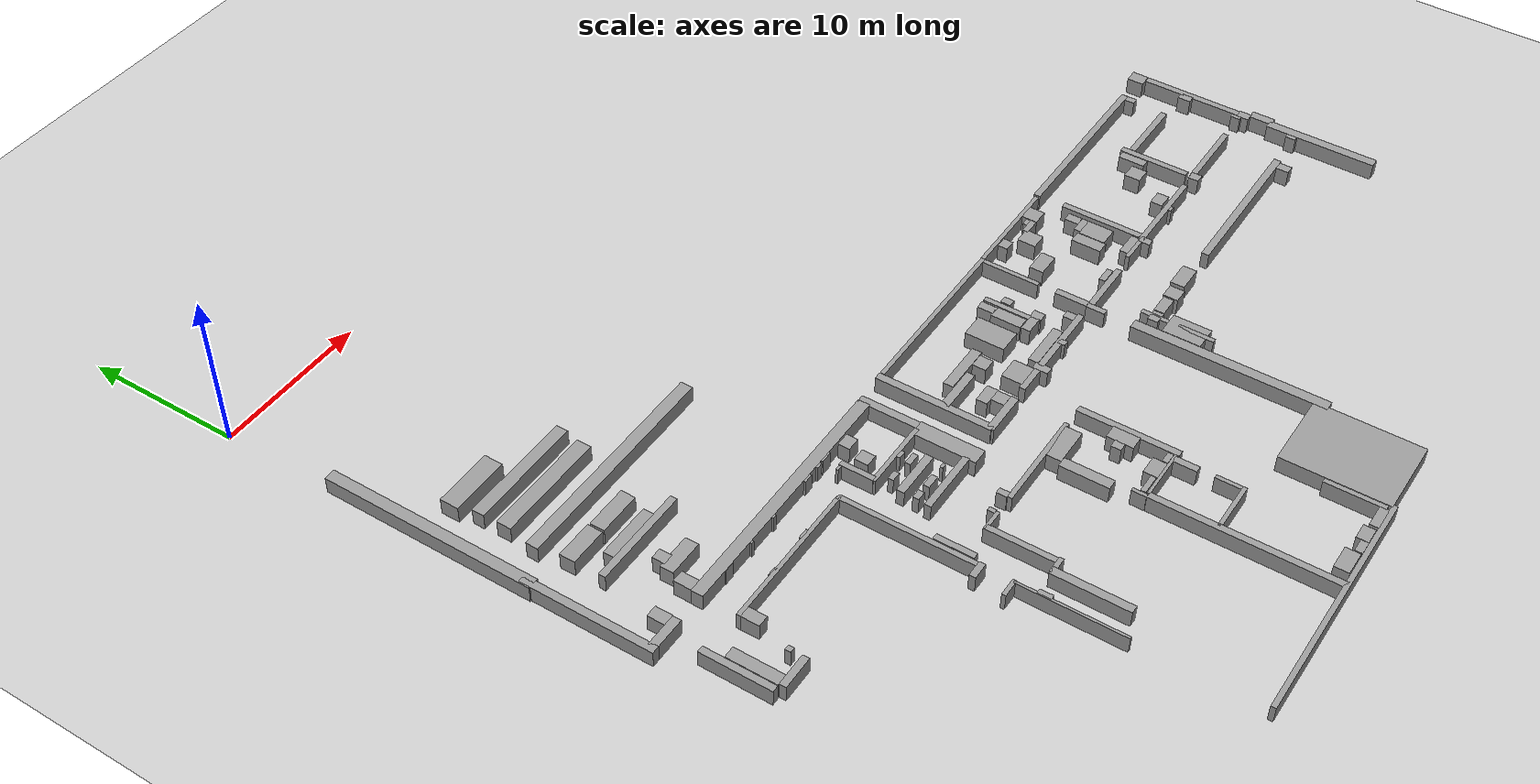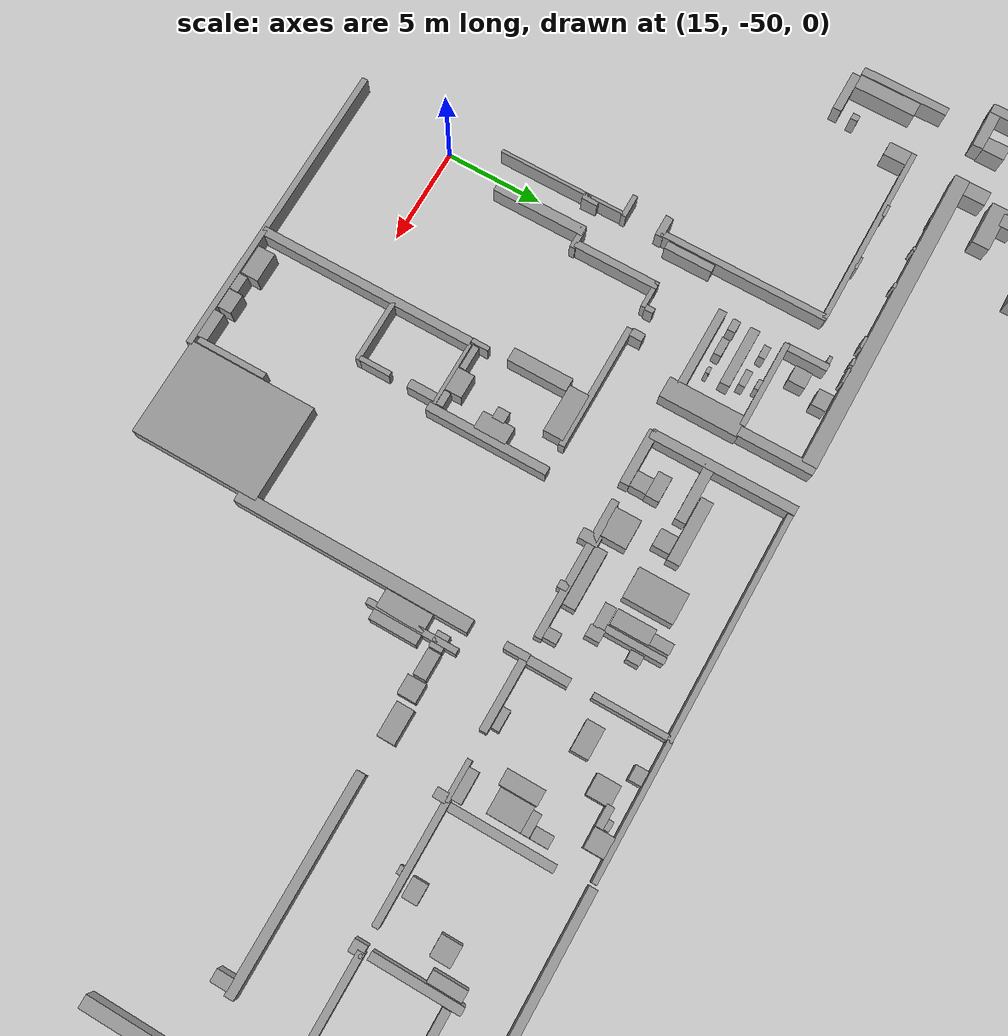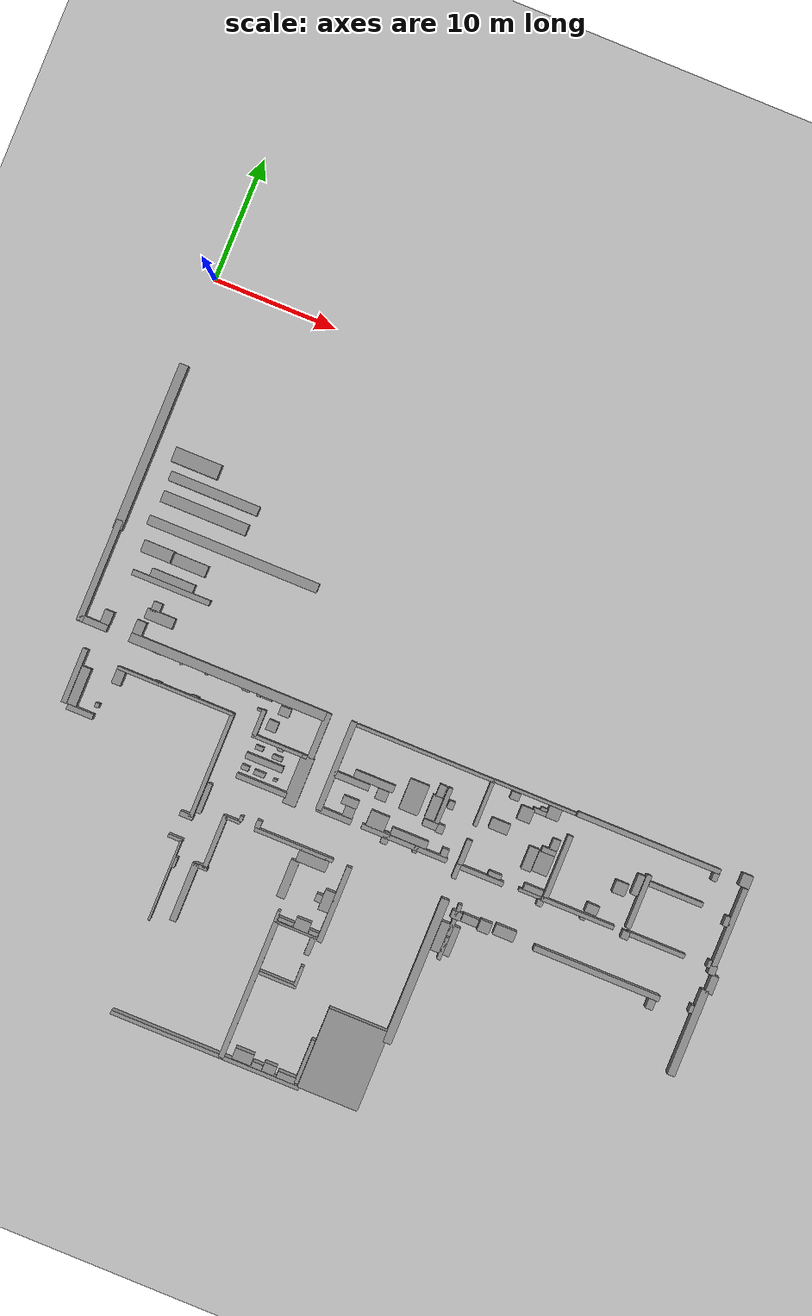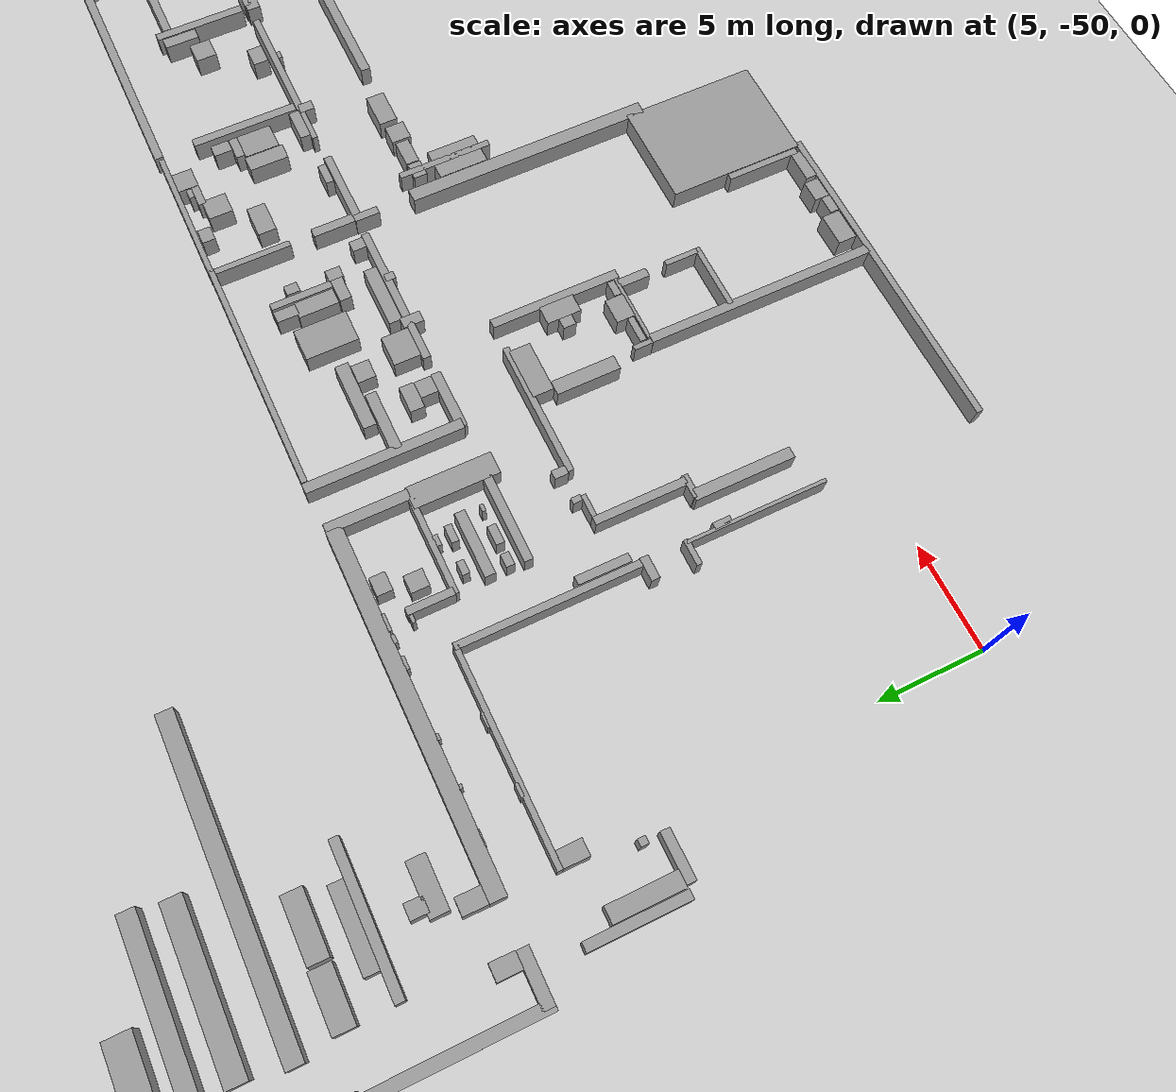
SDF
<?xml version="1.0" ?>
<sdf version='1.4'>
  <world name='default'>
    <light name='sun' type='directional'>
      <cast_shadows>1</cast_shadows>
      <pose>0 0 10 0 -0 0</pose>
      <diffuse>0.8 0.8 0.8 1</diffuse>
      <specular>0.2 0.2 0.2 1</specular>
      <attenuation>
        <range>1000</range>
        <constant>0.9</constant>
        <linear>0.01</linear>
        <quadratic>0.001</quadratic>
      </attenuation>
      <direction>-0.5 0.1 -0.9</direction>
    </light>

    <model name='ground_plane'>
      <static>1</static>
      <link name='link'>
        <collision name='collision'>
          <geometry>
            <plane>
              <normal>0 0 1</normal>
              <size>300 300</size>
            </plane>
          </geometry>
          <surface>
            <friction>
              <ode>
                <mu>100</mu>
                <mu2>50</mu2>
              </ode>
            </friction>
            <bounce/>
            <contact>
              <ode/>
            </contact>
          </surface>
          <max_contacts>10</max_contacts>
        </collision>
        <visual name='visual'>
          <cast_shadows>0</cast_shadows>
          <geometry>
            <plane>
              <normal>0 0 1</normal>
              <size>300 300</size>
            </plane>
          </geometry>
          <material>
            <script>
              <uri>file://media/materials/scripts/gazebo.material</uri>
              <name>Gazebo/Grey</name>
            </script>
          </material>
        </visual>
        <velocity_decay>
          <linear>0</linear>
          <angular>0</angular>
        </velocity_decay>
        <self_collide>0</self_collide>
        <kinematic>0</kinematic>
        <gravity>1</gravity>
      </link>
    </model>
    <physics type='ode'>
      <max_step_size>0.001</max_step_size>
      <real_time_factor>1</real_time_factor>
      <real_time_update_rate>1000</real_time_update_rate>
      <gravity>0 0 -9.8</gravity>
    </physics>
    <scene>
      <ambient>0.4 0.4 0.4 1</ambient>
      <background>0.7 0.7 0.7 1</background>
      <shadows>1</shadows>
    </scene>
    <spherical_coordinates>
      <surface_model>EARTH_WGS84</surface_model>
      <latitude_deg>0</latitude_deg>
      <longitude_deg>0</longitude_deg>
      <elevation>0</elevation>
      <heading_deg>0</heading_deg>
    </spherical_coordinates>

      <model name="wall_rect3549">
      <static>1</static>
      <link name='link'>
        <pose>0.3355228053052943 -24.17355341555266 0 0 -0 0</pose>
        <collision name='collision'>
          <geometry>
            <box>
              <size>0.51425949219405 8.382429670205694 2.0</size>
            </box>
          </geometry>
          <max_contacts>10</max_contacts>
          <surface>
            <bounce/>
            <friction>
              <ode/>
            </friction>
            <contact>
              <ode/>
            </contact>
          </surface>
        </collision>
        <visual name='visual'>
          <cast_shadows>0</cast_shadows>
          <geometry>
            <box>
              <size>0.51425949219405 8.382429670205694 2.0</size>
            </box>
          </geometry>
          <material>
            <script>
              <uri>model://grey_wall/materials/scripts</uri>
              <uri>model://grey_wall/materials/textures</uri>
              <name>vrc/grey_wall</name>
            </script>
          </material>
        </visual>
        <velocity_decay>
          <linear>0</linear>
          <angular>0</angular>
        </velocity_decay>
        <self_collide>0</self_collide>
        <kinematic>0</kinematic>
        <gravity>1</gravity>
      </link>
      <pose>0 0 0 0 -0 0</pose>
    </model>

      <model name="wall_rect3551">
      <static>1</static>
      <link name='link'>
        <pose>1.4128834767488212 -28.0947834555603 0 0 -0 0</pose>
        <collision name='collision'>
          <geometry>
            <box>
              <size>2.308999173986113 0.5399724700435873 2.0</size>
            </box>
          </geometry>
          <max_contacts>10</max_contacts>
          <surface>
            <bounce/>
            <friction>
              <ode/>
            </friction>
            <contact>
              <ode/>
            </contact>
          </surface>
        </collision>
        <visual name='visual'>
          <cast_shadows>0</cast_shadows>
          <geometry>
            <box>
              <size>2.308999173986113 0.5399724700435873 2.0</size>
            </box>
          </geometry>
          <material>
            <script>
              <uri>model://grey_wall/materials/scripts</uri>
              <uri>model://grey_wall/materials/textures</uri>
              <name>vrc/grey_wall</name>
            </script>
          </material>
        </visual>
        <velocity_decay>
          <linear>0</linear>
          <angular>0</angular>
        </velocity_decay>
        <self_collide>0</self_collide>
        <kinematic>0</kinematic>
        <gravity>1</gravity>
      </link>
      <pose>0 0 0 0 -0 0</pose>
    </model>

      <model name="wall_rect3553">
      <static>1</static>
      <link name='link'>
        <pose>12.551124197483915 -28.017644500412786 0 0 -0 0</pose>
        <collision name='collision'>
          <geometry>
            <box>
              <size>16.246724077019657 0.7456762064442906 2.0</size>
            </box>
          </geometry>
          <max_contacts>10</max_contacts>
          <surface>
            <bounce/>
            <friction>
              <ode/>
            </friction>
            <contact>
              <ode/>
            </contact>
          </surface>
        </collision>
        <visual name='visual'>
          <cast_shadows>0</cast_shadows>
          <geometry>
            <box>
              <size>16.246724077019657 0.7456762064442906 2.0</size>
            </box>
          </geometry>
          <material>
            <script>
              <uri>model://grey_wall/materials/scripts</uri>
              <uri>model://grey_wall/materials/textures</uri>
              <name>vrc/grey_wall</name>
            </script>
          </material>
        </visual>
        <velocity_decay>
          <linear>0</linear>
          <angular>0</angular>
        </velocity_decay>
        <self_collide>0</self_collide>
        <kinematic>0</kinematic>
        <gravity>1</gravity>
      </link>
      <pose>0 0 0 0 -0 0</pose>
    </model>

      <model name="wall_rect3555">
      <static>1</static>
      <link name='link'>
        <pose>9.212926984130641 -30.550371205874438 0 0 -0 0</pose>
        <collision name='collision'>
          <geometry>
            <box>
              <size>9.603795560087166 0.25712974249720855 2.0</size>
            </box>
          </geometry>
          <max_contacts>10</max_contacts>
          <surface>
            <bounce/>
            <friction>
              <ode/>
            </friction>
            <contact>
              <ode/>
            </contact>
          </surface>
        </collision>
        <visual name='visual'>
          <cast_shadows>0</cast_shadows>
          <geometry>
            <box>
              <size>9.603795560087166 0.25712974249720855 2.0</size>
            </box>
          </geometry>
          <material>
            <script>
              <uri>model://grey_wall/materials/scripts</uri>
              <uri>model://grey_wall/materials/textures</uri>
              <name>vrc/grey_wall</name>
            </script>
          </material>
        </visual>
        <velocity_decay>
          <linear>0</linear>
          <angular>0</angular>
        </velocity_decay>
        <self_collide>0</self_collide>
        <kinematic>0</kinematic>
        <gravity>1</gravity>
      </link>
      <pose>0 0 0 0 -0 0</pose>
    </model>

      <model name="wall_rect3557">
      <static>1</static>
      <link name='link'>
        <pose>1.608315158459961 -32.37599107447106 0 0 -0 0</pose>
        <collision name='collision'>
          <geometry>
            <box>
              <size>0.4371205874439697 4.4740575986473905 2.0</size>
            </box>
          </geometry>
          <max_contacts>10</max_contacts>
          <surface>
            <bounce/>
            <friction>
              <ode/>
            </friction>
            <contact>
              <ode/>
            </contact>
          </surface>
        </collision>
        <visual name='visual'>
          <cast_shadows>0</cast_shadows>
          <geometry>
            <box>
              <size>0.4371205874439697 4.4740575986473905 2.0</size>
            </box>
          </geometry>
          <material>
            <script>
              <uri>model://grey_wall/materials/scripts</uri>
              <uri>model://grey_wall/materials/textures</uri>
              <name>vrc/grey_wall</name>
            </script>
          </material>
        </visual>
        <velocity_decay>
          <linear>0</linear>
          <angular>0</angular>
        </velocity_decay>
        <self_collide>0</self_collide>
        <kinematic>0</kinematic>
        <gravity>1</gravity>
      </link>
      <pose>0 0 0 0 -0 0</pose>
    </model>

      <model name="wall_rect3559">
      <static>1</static>
      <link name='link'>
        <pose>2.235430984786672 -33.01002779274302 0 0 -0 0</pose>
        <collision name='collision'>
          <geometry>
            <box>
              <size>0.7506231462295126 3.1391887036031356 2.0</size>
            </box>
          </geometry>
          <max_contacts>10</max_contacts>
          <surface>
            <bounce/>
            <friction>
              <ode/>
            </friction>
            <contact>
              <ode/>
            </contact>
          </surface>
        </collision>
        <visual name='visual'>
          <cast_shadows>0</cast_shadows>
          <geometry>
            <box>
              <size>0.7506231462295126 3.1391887036031356 2.0</size>
            </box>
          </geometry>
          <material>
            <script>
              <uri>model://grey_wall/materials/scripts</uri>
              <uri>model://grey_wall/materials/textures</uri>
              <name>vrc/grey_wall</name>
            </script>
          </material>
        </visual>
        <velocity_decay>
          <linear>0</linear>
          <angular>0</angular>
        </velocity_decay>
        <self_collide>0</self_collide>
        <kinematic>0</kinematic>
        <gravity>1</gravity>
      </link>
      <pose>0 0 0 0 -0 0</pose>
    </model>

      <model name="wall_rect3561">
      <static>1</static>
      <link name='link'>
        <pose>4.7867030267328845 -31.250355715864185 0 0 -0 0</pose>
        <collision name='collision'>
          <geometry>
            <box>
              <size>0.7456762064442906 1.141013234581248 2.0</size>
            </box>
          </geometry>
          <max_contacts>10</max_contacts>
          <surface>
            <bounce/>
            <friction>
              <ode/>
            </friction>
            <contact>
              <ode/>
            </contact>
          </surface>
        </collision>
        <visual name='visual'>
          <cast_shadows>0</cast_shadows>
          <geometry>
            <box>
              <size>0.7456762064442906 1.141013234581248 2.0</size>
            </box>
          </geometry>
          <material>
            <script>
              <uri>model://grey_wall/materials/scripts</uri>
              <uri>model://grey_wall/materials/textures</uri>
              <name>vrc/grey_wall</name>
            </script>
          </material>
        </visual>
        <velocity_decay>
          <linear>0</linear>
          <angular>0</angular>
        </velocity_decay>
        <self_collide>0</self_collide>
        <kinematic>0</kinematic>
        <gravity>1</gravity>
      </link>
      <pose>0 0 0 0 -0 0</pose>
    </model>

      <model name="wall_rect3563">
      <static>1</static>
      <link name='link'>
        <pose>4.829589656200969 -27.093271388651523 0 0 -0 0</pose>
        <collision name='collision'>
          <geometry>
            <box>
              <size>0.7713892634897902 1.1056578531400154 2.0</size>
            </box>
          </geometry>
          <max_contacts>10</max_contacts>
          <surface>
            <bounce/>
            <friction>
              <ode/>
            </friction>
            <contact>
              <ode/>
            </contact>
          </surface>
        </collision>
        <visual name='visual'>
          <cast_shadows>0</cast_shadows>
          <geometry>
            <box>
              <size>0.7713892634897902 1.1056578531400154 2.0</size>
            </box>
          </geometry>
          <material>
            <script>
              <uri>model://grey_wall/materials/scripts</uri>
              <uri>model://grey_wall/materials/textures</uri>
              <name>vrc/grey_wall</name>
            </script>
          </material>
        </visual>
        <velocity_decay>
          <linear>0</linear>
          <angular>0</angular>
        </velocity_decay>
        <self_collide>0</self_collide>
        <kinematic>0</kinematic>
        <gravity>1</gravity>
      </link>
      <pose>0 0 0 0 -0 0</pose>
    </model>

      <model name="wall_rect3565">
      <static>1</static>
      <link name='link'>
        <pose>2.2303731346561024 -27.28831880435408 0 0 -0 0</pose>
        <collision name='collision'>
          <geometry>
            <box>
              <size>0.7456762064442906 1.1056578531400154 2.0</size>
            </box>
          </geometry>
          <max_contacts>10</max_contacts>
          <surface>
            <bounce/>
            <friction>
              <ode/>
            </friction>
            <contact>
              <ode/>
            </contact>
          </surface>
        </collision>
        <visual name='visual'>
          <cast_shadows>0</cast_shadows>
          <geometry>
            <box>
              <size>0.7456762064442906 1.1056578531400154 2.0</size>
            </box>
          </geometry>
          <material>
            <script>
              <uri>model://grey_wall/materials/scripts</uri>
              <uri>model://grey_wall/materials/textures</uri>
              <name>vrc/grey_wall</name>
            </script>
          </material>
        </visual>
        <velocity_decay>
          <linear>0</linear>
          <angular>0</angular>
        </velocity_decay>
        <self_collide>0</self_collide>
        <kinematic>0</kinematic>
        <gravity>1</gravity>
      </link>
      <pose>0 0 0 0 -0 0</pose>
    </model>

      <model name="wall_rect3567">
      <static>1</static>
      <link name='link'>
        <pose>5.915773474205191 -23.313997835934334 0 0 -0 0</pose>
        <collision name='collision'>
          <geometry>
            <box>
              <size>6.428243598428378 0.4371205874439697 2.0</size>
            </box>
          </geometry>
          <max_contacts>10</max_contacts>
          <surface>
            <bounce/>
            <friction>
              <ode/>
            </friction>
            <contact>
              <ode/>
            </contact>
          </surface>
        </collision>
        <visual name='visual'>
          <cast_shadows>0</cast_shadows>
          <geometry>
            <box>
              <size>6.428243598428378 0.4371205874439697 2.0</size>
            </box>
          </geometry>
          <material>
            <script>
              <uri>model://grey_wall/materials/scripts</uri>
              <uri>model://grey_wall/materials/textures</uri>
              <name>vrc/grey_wall</name>
            </script>
          </material>
        </visual>
        <velocity_decay>
          <linear>0</linear>
          <angular>0</angular>
        </velocity_decay>
        <self_collide>0</self_collide>
        <kinematic>0</kinematic>
        <gravity>1</gravity>
      </link>
      <pose>0 0 0 0 -0 0</pose>
    </model>

      <model name="wall_rect3569">
      <static>1</static>
      <link name='link'>
        <pose>5.812007828592867 -22.76557894732295 0 0 -0 0</pose>
        <collision name='collision'>
          <geometry>
            <box>
              <size>3.5741034819080784 0.6685373304927421 2.0</size>
            </box>
          </geometry>
          <max_contacts>10</max_contacts>
          <surface>
            <bounce/>
            <friction>
              <ode/>
            </friction>
            <contact>
              <ode/>
            </contact>
          </surface>
        </collision>
        <visual name='visual'>
          <cast_shadows>0</cast_shadows>
          <geometry>
            <box>
              <size>3.5741034819080784 0.6685373304927421 2.0</size>
            </box>
          </geometry>
          <material>
            <script>
              <uri>model://grey_wall/materials/scripts</uri>
              <uri>model://grey_wall/materials/textures</uri>
              <name>vrc/grey_wall</name>
            </script>
          </material>
        </visual>
        <velocity_decay>
          <linear>0</linear>
          <angular>0</angular>
        </velocity_decay>
        <self_collide>0</self_collide>
        <kinematic>0</kinematic>
        <gravity>1</gravity>
      </link>
      <pose>0 0 0 0 -0 0</pose>
    </model>

      <model name="wall_rect3582">
      <static>1</static>
      <link name='link'>
        <pose>3.8804151049162914 -21.13242839227085 0 0 -0 0</pose>
        <collision name='collision'>
          <geometry>
            <box>
              <size>2.442732499726234 0.9770929998904935 2.0</size>
            </box>
          </geometry>
          <max_contacts>10</max_contacts>
          <surface>
            <bounce/>
            <friction>
              <ode/>
            </friction>
            <contact>
              <ode/>
            </contact>
          </surface>
        </collision>
        <visual name='visual'>
          <cast_shadows>0</cast_shadows>
          <geometry>
            <box>
              <size>2.442732499726234 0.9770929998904935 2.0</size>
            </box>
          </geometry>
          <material>
            <script>
              <uri>model://grey_wall/materials/scripts</uri>
              <uri>model://grey_wall/materials/textures</uri>
              <name>vrc/grey_wall</name>
            </script>
          </material>
        </visual>
        <velocity_decay>
          <linear>0</linear>
          <angular>0</angular>
        </velocity_decay>
        <self_collide>0</self_collide>
        <kinematic>0</kinematic>
        <gravity>1</gravity>
      </link>
      <pose>0 0 0 0 -0 0</pose>
    </model>

      <model name="wall_rect3584">
      <static>1</static>
      <link name='link'>
        <pose>6.6126079827946045 -21.16255144047736 0 0 -0 0</pose>
        <collision name='collision'>
          <geometry>
            <box>
              <size>2.7770013773617763 0.925667029792153 2.0</size>
            </box>
          </geometry>
          <max_contacts>10</max_contacts>
          <surface>
            <bounce/>
            <friction>
              <ode/>
            </friction>
            <contact>
              <ode/>
            </contact>
          </surface>
        </collision>
        <visual name='visual'>
          <cast_shadows>0</cast_shadows>
          <geometry>
            <box>
              <size>2.7770013773617763 0.925667029792153 2.0</size>
            </box>
          </geometry>
          <material>
            <script>
              <uri>model://grey_wall/materials/scripts</uri>
              <uri>model://grey_wall/materials/textures</uri>
              <name>vrc/grey_wall</name>
            </script>
          </material>
        </visual>
        <velocity_decay>
          <linear>0</linear>
          <angular>0</angular>
        </velocity_decay>
        <self_collide>0</self_collide>
        <kinematic>0</kinematic>
        <gravity>1</gravity>
      </link>
      <pose>0 0 0 0 -0 0</pose>
    </model>

      <model name="wall_rect3586">
      <static>1</static>
      <link name='link'>
        <pose>16.12328997018416 -30.383238512967655 0 0 -0 0</pose>
        <collision name='collision'>
          <geometry>
            <box>
              <size>0.35998164669572486 2.134176895125179 2.0</size>
            </box>
          </geometry>
          <max_contacts>10</max_contacts>
          <surface>
            <bounce/>
            <friction>
              <ode/>
            </friction>
            <contact>
              <ode/>
            </contact>
          </surface>
        </collision>
        <visual name='visual'>
          <cast_shadows>0</cast_shadows>
          <geometry>
            <box>
              <size>0.35998164669572486 2.134176895125179 2.0</size>
            </box>
          </geometry>
          <material>
            <script>
              <uri>model://grey_wall/materials/scripts</uri>
              <uri>model://grey_wall/materials/textures</uri>
              <name>vrc/grey_wall</name>
            </script>
          </material>
        </visual>
        <velocity_decay>
          <linear>0</linear>
          <angular>0</angular>
        </velocity_decay>
        <self_collide>0</self_collide>
        <kinematic>0</kinematic>
        <gravity>1</gravity>
      </link>
      <pose>0 0 0 0 -0 0</pose>
    </model>

      <model name="wall_rect3588">
      <static>1</static>
      <link name='link'>
        <pose>17.64035551211457 -28.853315902542022 0 0 -0 0</pose>
        <collision name='collision'>
          <geometry>
            <box>
              <size>0.8742412036864713 0.7199632933914497 2.0</size>
            </box>
          </geometry>
          <max_contacts>10</max_contacts>
          <surface>
            <bounce/>
            <friction>
              <ode/>
            </friction>
            <contact>
              <ode/>
            </contact>
          </surface>
        </collision>
        <visual name='visual'>
          <cast_shadows>0</cast_shadows>
          <geometry>
            <box>
              <size>0.8742412036864713 0.7199632933914497 2.0</size>
            </box>
          </geometry>
          <material>
            <script>
              <uri>model://grey_wall/materials/scripts</uri>
              <uri>model://grey_wall/materials/textures</uri>
              <name>vrc/grey_wall</name>
            </script>
          </material>
        </visual>
        <velocity_decay>
          <linear>0</linear>
          <angular>0</angular>
        </velocity_decay>
        <self_collide>0</self_collide>
        <kinematic>0</kinematic>
        <gravity>1</gravity>
      </link>
      <pose>0 0 0 0 -0 0</pose>
    </model>

      <model name="wall_rect3590">
      <static>1</static>
      <link name='link'>
        <pose>17.151809084165652 -30.22896035068548 0 0 -0 0</pose>
        <collision name='collision'>
          <geometry>
            <box>
              <size>0.8228152335881308 0.8485281466409716 2.0</size>
            </box>
          </geometry>
          <max_contacts>10</max_contacts>
          <surface>
            <bounce/>
            <friction>
              <ode/>
            </friction>
            <contact>
              <ode/>
            </contact>
          </surface>
        </collision>
        <visual name='visual'>
          <cast_shadows>0</cast_shadows>
          <geometry>
            <box>
              <size>0.8228152335881308 0.8485281466409716 2.0</size>
            </box>
          </geometry>
          <material>
            <script>
              <uri>model://grey_wall/materials/scripts</uri>
              <uri>model://grey_wall/materials/textures</uri>
              <name>vrc/grey_wall</name>
            </script>
          </material>
        </visual>
        <velocity_decay>
          <linear>0</linear>
          <angular>0</angular>
        </velocity_decay>
        <self_collide>0</self_collide>
        <kinematic>0</kinematic>
        <gravity>1</gravity>
      </link>
      <pose>0 0 0 0 -0 0</pose>
    </model>

      <model name="wall_rect3592">
      <static>1</static>
      <link name='link'>
        <pose>17.640354972142102 -33.05738726976743 0 0 -0 0</pose>
        <collision name='collision'>
          <geometry>
            <box>
              <size>3.0855569819628315 0.4885465071448797 2.0</size>
            </box>
          </geometry>
          <max_contacts>10</max_contacts>
          <surface>
            <bounce/>
            <friction>
              <ode/>
            </friction>
            <contact>
              <ode/>
            </contact>
          </surface>
        </collision>
        <visual name='visual'>
          <cast_shadows>0</cast_shadows>
          <geometry>
            <box>
              <size>3.0855569819628315 0.4885465071448797 2.0</size>
            </box>
          </geometry>
          <material>
            <script>
              <uri>model://grey_wall/materials/scripts</uri>
              <uri>model://grey_wall/materials/textures</uri>
              <name>vrc/grey_wall</name>
            </script>
          </material>
        </visual>
        <velocity_decay>
          <linear>0</linear>
          <angular>0</angular>
        </velocity_decay>
        <self_collide>0</self_collide>
        <kinematic>0</kinematic>
        <gravity>1</gravity>
      </link>
      <pose>0 0 0 0 -0 0</pose>
    </model>

      <model name="wall_rect3594">
      <static>1</static>
      <link name='link'>
        <pose>13.976255650181932 -34.76729994397965 0 0 -0 0</pose>
        <collision name='collision'>
          <geometry>
            <box>
              <size>0.3342686688461875 8.588133262613738 2.0</size>
            </box>
          </geometry>
          <max_contacts>10</max_contacts>
          <surface>
            <bounce/>
            <friction>
              <ode/>
            </friction>
            <contact>
              <ode/>
            </contact>
          </surface>
        </collision>
        <visual name='visual'>
          <cast_shadows>0</cast_shadows>
          <geometry>
            <box>
              <size>0.3342686688461875 8.588133262613738 2.0</size>
            </box>
          </geometry>
          <material>
            <script>
              <uri>model://grey_wall/materials/scripts</uri>
              <uri>model://grey_wall/materials/textures</uri>
              <name>vrc/grey_wall</name>
            </script>
          </material>
        </visual>
        <velocity_decay>
          <linear>0</linear>
          <angular>0</angular>
        </velocity_decay>
        <self_collide>0</self_collide>
        <kinematic>0</kinematic>
        <gravity>1</gravity>
      </link>
      <pose>0 0 0 0 -0 0</pose>
    </model>

      <model name="wall_rect3596">
      <static>1</static>
      <link name='link'>
        <pose>18.090332642480554 -34.76729907642389 0 0 -0 0</pose>
        <collision name='collision'>
          <geometry>
            <box>
              <size>4.139788937000836 0.41140760959443246 2.0</size>
            </box>
          </geometry>
          <max_contacts>10</max_contacts>
          <surface>
            <bounce/>
            <friction>
              <ode/>
            </friction>
            <contact>
              <ode/>
            </contact>
          </surface>
        </collision>
        <visual name='visual'>
          <cast_shadows>0</cast_shadows>
          <geometry>
            <box>
              <size>4.139788937000836 0.41140760959443246 2.0</size>
            </box>
          </geometry>
          <material>
            <script>
              <uri>model://grey_wall/materials/scripts</uri>
              <uri>model://grey_wall/materials/textures</uri>
              <name>vrc/grey_wall</name>
            </script>
          </material>
        </visual>
        <velocity_decay>
          <linear>0</linear>
          <angular>0</angular>
        </velocity_decay>
        <self_collide>0</self_collide>
        <kinematic>0</kinematic>
        <gravity>1</gravity>
      </link>
      <pose>0 0 0 0 -0 0</pose>
    </model>

      <model name="wall_rect3598">
      <static>1</static>
      <link name='link'>
        <pose>16.431845657580993 -33.983053032424195 0 0 -0 0</pose>
        <collision name='collision'>
          <geometry>
            <box>
              <size>0.6171113747936674 0.3856946245452622 2.0</size>
            </box>
          </geometry>
          <max_contacts>10</max_contacts>
          <surface>
            <bounce/>
            <friction>
              <ode/>
            </friction>
            <contact>
              <ode/>
            </contact>
          </surface>
        </collision>
        <visual name='visual'>
          <cast_shadows>0</cast_shadows>
          <geometry>
            <box>
              <size>0.6171113747936674 0.3856946245452622 2.0</size>
            </box>
          </geometry>
          <material>
            <script>
              <uri>model://grey_wall/materials/scripts</uri>
              <uri>model://grey_wall/materials/textures</uri>
              <name>vrc/grey_wall</name>
            </script>
          </material>
        </visual>
        <velocity_decay>
          <linear>0</linear>
          <angular>0</angular>
        </velocity_decay>
        <self_collide>0</self_collide>
        <kinematic>0</kinematic>
        <gravity>1</gravity>
      </link>
      <pose>0 0 0 0 -0 0</pose>
    </model>

      <model name="wall_rect3600">
      <static>1</static>
      <link name='link'>
        <pose>17.627498479617515 -34.00876796137426 0 0 -0 0</pose>
        <collision name='collision'>
          <geometry>
            <box>
              <size>0.8999541167393121 0.3856946245452622 2.0</size>
            </box>
          </geometry>
          <max_contacts>10</max_contacts>
          <surface>
            <bounce/>
            <friction>
              <ode/>
            </friction>
            <contact>
              <ode/>
            </contact>
          </surface>
        </collision>
        <visual name='visual'>
          <cast_shadows>0</cast_shadows>
          <geometry>
            <box>
              <size>0.8999541167393121 0.3856946245452622 2.0</size>
            </box>
          </geometry>
          <material>
            <script>
              <uri>model://grey_wall/materials/scripts</uri>
              <uri>model://grey_wall/materials/textures</uri>
              <name>vrc/grey_wall</name>
            </script>
          </material>
        </visual>
        <velocity_decay>
          <linear>0</linear>
          <angular>0</angular>
        </velocity_decay>
        <self_collide>0</self_collide>
        <kinematic>0</kinematic>
        <gravity>1</gravity>
      </link>
      <pose>0 0 0 0 -0 0</pose>
    </model>

      <model name="wall_rect3602">
      <static>1</static>
      <link name='link'>
        <pose>18.938858956814947 -34.008764977126404 0 0 -0 0</pose>
        <collision name='collision'>
          <geometry>
            <box>
              <size>0.3342686688461875 0.17999082334786243 2.0</size>
            </box>
          </geometry>
          <max_contacts>10</max_contacts>
          <surface>
            <bounce/>
            <friction>
              <ode/>
            </friction>
            <contact>
              <ode/>
            </contact>
          </surface>
        </collision>
        <visual name='visual'>
          <cast_shadows>0</cast_shadows>
          <geometry>
            <box>
              <size>0.3342686688461875 0.17999082334786243 2.0</size>
            </box>
          </geometry>
          <material>
            <script>
              <uri>model://grey_wall/materials/scripts</uri>
              <uri>model://grey_wall/materials/textures</uri>
              <name>vrc/grey_wall</name>
            </script>
          </material>
        </visual>
        <velocity_decay>
          <linear>0</linear>
          <angular>0</angular>
        </velocity_decay>
        <self_collide>0</self_collide>
        <kinematic>0</kinematic>
        <gravity>1</gravity>
      </link>
      <pose>0 0 0 0 -0 0</pose>
    </model>

      <model name="wall_rect3604">
      <static>1</static>
      <link name='link'>
        <pose>16.88182283834441 -32.1831467500461 0 0 -0 0</pose>
        <collision name='collision'>
          <geometry>
            <box>
              <size>0.6428243886413696 0.3342686688461875 2.0</size>
            </box>
          </geometry>
          <max_contacts>10</max_contacts>
          <surface>
            <bounce/>
            <friction>
              <ode/>
            </friction>
            <contact>
              <ode/>
            </contact>
          </surface>
        </collision>
        <visual name='visual'>
          <cast_shadows>0</cast_shadows>
          <geometry>
            <box>
              <size>0.6428243886413696 0.3342686688461875 2.0</size>
            </box>
          </geometry>
          <material>
            <script>
              <uri>model://grey_wall/materials/scripts</uri>
              <uri>model://grey_wall/materials/textures</uri>
              <name>vrc/grey_wall</name>
            </script>
          </material>
        </visual>
        <velocity_decay>
          <linear>0</linear>
          <angular>0</angular>
        </velocity_decay>
        <self_collide>0</self_collide>
        <kinematic>0</kinematic>
        <gravity>1</gravity>
      </link>
      <pose>0 0 0 0 -0 0</pose>
    </model>

      <model name="wall_rect3606">
      <static>1</static>
      <link name='link'>
        <pose>18.437457616660872 -32.363137573393956 0 0 -0 0</pose>
        <collision name='collision'>
          <geometry>
            <box>
              <size>0.8228152335881308 0.3342686688461875 2.0</size>
            </box>
          </geometry>
          <max_contacts>10</max_contacts>
          <surface>
            <bounce/>
            <friction>
              <ode/>
            </friction>
            <contact>
              <ode/>
            </contact>
          </surface>
        </collision>
        <visual name='visual'>
          <cast_shadows>0</cast_shadows>
          <geometry>
            <box>
              <size>0.8228152335881308 0.3342686688461875 2.0</size>
            </box>
          </geometry>
          <material>
            <script>
              <uri>model://grey_wall/materials/scripts</uri>
              <uri>model://grey_wall/materials/textures</uri>
              <name>vrc/grey_wall</name>
            </script>
          </material>
        </visual>
        <velocity_decay>
          <linear>0</linear>
          <angular>0</angular>
        </velocity_decay>
        <self_collide>0</self_collide>
        <kinematic>0</kinematic>
        <gravity>1</gravity>
      </link>
      <pose>0 0 0 0 -0 0</pose>
    </model>

      <model name="wall_rect3608">
      <static>1</static>
      <link name='link'>
        <pose>18.411744311228038 -31.694597244254098 0 0 -0 0</pose>
        <collision name='collision'>
          <geometry>
            <box>
              <size>0.51425949219405 0.23141676464767122 2.0</size>
            </box>
          </geometry>
          <max_contacts>10</max_contacts>
          <surface>
            <bounce/>
            <friction>
              <ode/>
            </friction>
            <contact>
              <ode/>
            </contact>
          </surface>
        </collision>
        <visual name='visual'>
          <cast_shadows>0</cast_shadows>
          <geometry>
            <box>
              <size>0.51425949219405 0.23141676464767122 2.0</size>
            </box>
          </geometry>
          <material>
            <script>
              <uri>model://grey_wall/materials/scripts</uri>
              <uri>model://grey_wall/materials/textures</uri>
              <name>vrc/grey_wall</name>
            </script>
          </material>
        </visual>
        <velocity_decay>
          <linear>0</linear>
          <angular>0</angular>
        </velocity_decay>
        <self_collide>0</self_collide>
        <kinematic>0</kinematic>
        <gravity>1</gravity>
      </link>
      <pose>0 0 0 0 -0 0</pose>
    </model>

      <model name="wall_rect3610">
      <static>1</static>
      <link name='link'>
        <pose>18.244609508828802 -31.463181815138338 0 0 -0 0</pose>
        <collision name='collision'>
          <geometry>
            <box>
              <size>4.55119662579123 0.28284272754637874 2.0</size>
            </box>
          </geometry>
          <max_contacts>10</max_contacts>
          <surface>
            <bounce/>
            <friction>
              <ode/>
            </friction>
            <contact>
              <ode/>
            </contact>
          </surface>
        </collision>
        <visual name='visual'>
          <cast_shadows>0</cast_shadows>
          <geometry>
            <box>
              <size>4.55119662579123 0.28284272754637874 2.0</size>
            </box>
          </geometry>
          <material>
            <script>
              <uri>model://grey_wall/materials/scripts</uri>
              <uri>model://grey_wall/materials/textures</uri>
              <name>vrc/grey_wall</name>
            </script>
          </material>
        </visual>
        <velocity_decay>
          <linear>0</linear>
          <angular>0</angular>
        </velocity_decay>
        <self_collide>0</self_collide>
        <kinematic>0</kinematic>
        <gravity>1</gravity>
      </link>
      <pose>0 0 0 0 -0 0</pose>
    </model>

      <model name="wall_rect3612">
      <static>1</static>
      <link name='link'>
        <pose>20.604230237925552 -33.38944780039335 0 0 -0 0</pose>
        <collision name='collision'>
          <geometry>
            <box>
              <size>1.0610062336581831 3.9810995236218876 2.0</size>
            </box>
          </geometry>
          <max_contacts>10</max_contacts>
          <surface>
            <bounce/>
            <friction>
              <ode/>
            </friction>
            <contact>
              <ode/>
            </contact>
          </surface>
        </collision>
        <visual name='visual'>
          <cast_shadows>0</cast_shadows>
          <geometry>
            <box>
              <size>1.0610062336581831 3.9810995236218876 2.0</size>
            </box>
          </geometry>
          <material>
            <script>
              <uri>model://grey_wall/materials/scripts</uri>
              <uri>model://grey_wall/materials/textures</uri>
              <name>vrc/grey_wall</name>
            </script>
          </material>
        </visual>
        <velocity_decay>
          <linear>0</linear>
          <angular>0</angular>
        </velocity_decay>
        <self_collide>0</self_collide>
        <kinematic>0</kinematic>
        <gravity>1</gravity>
      </link>
      <pose>0 0 0 0 -0 0</pose>
    </model>

      <model name="wall_rect3614">
      <static>1</static>
      <link name='link'>
        <pose>16.4447011277577 -40.128455958801396 0 0 -0 0</pose>
        <collision name='collision'>
          <geometry>
            <box>
              <size>0.3856946245452622 4.345492745397869 2.0</size>
            </box>
          </geometry>
          <max_contacts>10</max_contacts>
          <surface>
            <bounce/>
            <friction>
              <ode/>
            </friction>
            <contact>
              <ode/>
            </contact>
          </surface>
        </collision>
        <visual name='visual'>
          <cast_shadows>0</cast_shadows>
          <geometry>
            <box>
              <size>0.3856946245452622 4.345492745397869 2.0</size>
            </box>
          </geometry>
          <material>
            <script>
              <uri>model://grey_wall/materials/scripts</uri>
              <uri>model://grey_wall/materials/textures</uri>
              <name>vrc/grey_wall</name>
            </script>
          </material>
        </visual>
        <velocity_decay>
          <linear>0</linear>
          <angular>0</angular>
        </velocity_decay>
        <self_collide>0</self_collide>
        <kinematic>0</kinematic>
        <gravity>1</gravity>
      </link>
      <pose>0 0 0 0 -0 0</pose>
    </model>

      <model name="wall_rect3616">
      <static>1</static>
      <link name='link'>
        <pose>16.98467410537541 -38.0714179684263 0 0 -0 0</pose>
        <collision name='collision'>
          <geometry>
            <box>
              <size>1.4142136017337292 0.23141676464767122 2.0</size>
            </box>
          </geometry>
          <max_contacts>10</max_contacts>
          <surface>
            <bounce/>
            <friction>
              <ode/>
            </friction>
            <contact>
              <ode/>
            </contact>
          </surface>
        </collision>
        <visual name='visual'>
          <cast_shadows>0</cast_shadows>
          <geometry>
            <box>
              <size>1.4142136017337292 0.23141676464767122 2.0</size>
            </box>
          </geometry>
          <material>
            <script>
              <uri>model://grey_wall/materials/scripts</uri>
              <uri>model://grey_wall/materials/textures</uri>
              <name>vrc/grey_wall</name>
            </script>
          </material>
        </visual>
        <velocity_decay>
          <linear>0</linear>
          <angular>0</angular>
        </velocity_decay>
        <self_collide>0</self_collide>
        <kinematic>0</kinematic>
        <gravity>1</gravity>
      </link>
      <pose>0 0 0 0 -0 0</pose>
    </model>

      <model name="wall_rect3618">
      <static>1</static>
      <link name='link'>
        <pose>22.15389629375136 -38.084272499050904 0 0 -0 0</pose>
        <collision name='collision'>
          <geometry>
            <box>
              <size>6.507209892410845 0.30855568379701726 2.0</size>
            </box>
          </geometry>
          <max_contacts>10</max_contacts>
          <surface>
            <bounce/>
            <friction>
              <ode/>
            </friction>
            <contact>
              <ode/>
            </contact>
          </surface>
        </collision>
        <visual name='visual'>
          <cast_shadows>0</cast_shadows>
          <geometry>
            <box>
              <size>6.507209892410845 0.30855568379701726 2.0</size>
            </box>
          </geometry>
          <material>
            <script>
              <uri>model://grey_wall/materials/scripts</uri>
              <uri>model://grey_wall/materials/textures</uri>
              <name>vrc/grey_wall</name>
            </script>
          </material>
        </visual>
        <velocity_decay>
          <linear>0</linear>
          <angular>0</angular>
        </velocity_decay>
        <self_collide>0</self_collide>
        <kinematic>0</kinematic>
        <gravity>1</gravity>
      </link>
      <pose>0 0 0 0 -0 0</pose>
    </model>

      <model name="wall_rect3620">
      <static>1</static>
      <link name='link'>
        <pose>17.62749889359641 -37.73714632613171 0 0 -0 0</pose>
        <collision name='collision'>
          <geometry>
            <box>
              <size>0.28284272754637874 0.4371205874439697 2.0</size>
            </box>
          </geometry>
          <max_contacts>10</max_contacts>
          <surface>
            <bounce/>
            <friction>
              <ode/>
            </friction>
            <contact>
              <ode/>
            </contact>
          </surface>
        </collision>
        <visual name='visual'>
          <cast_shadows>0</cast_shadows>
          <geometry>
            <box>
              <size>0.28284272754637874 0.4371205874439697 2.0</size>
            </box>
          </geometry>
          <material>
            <script>
              <uri>model://grey_wall/materials/scripts</uri>
              <uri>model://grey_wall/materials/textures</uri>
              <name>vrc/grey_wall</name>
            </script>
          </material>
        </visual>
        <velocity_decay>
          <linear>0</linear>
          <angular>0</angular>
        </velocity_decay>
        <self_collide>0</self_collide>
        <kinematic>0</kinematic>
        <gravity>1</gravity>
      </link>
      <pose>0 0 0 0 -0 0</pose>
    </model>

      <model name="wall_rect3622">
      <static>1</static>
      <link name='link'>
        <pose>19.028854685272726 -37.63429679421225 0 0 -0 0</pose>
        <collision name='collision'>
          <geometry>
            <box>
              <size>0.41140760959443246 0.6428243886413696 2.0</size>
            </box>
          </geometry>
          <max_contacts>10</max_contacts>
          <surface>
            <bounce/>
            <friction>
              <ode/>
            </friction>
            <contact>
              <ode/>
            </contact>
          </surface>
        </collision>
        <visual name='visual'>
          <cast_shadows>0</cast_shadows>
          <geometry>
            <box>
              <size>0.41140760959443246 0.6428243886413696 2.0</size>
            </box>
          </geometry>
          <material>
            <script>
              <uri>model://grey_wall/materials/scripts</uri>
              <uri>model://grey_wall/materials/textures</uri>
              <name>vrc/grey_wall</name>
            </script>
          </material>
        </visual>
        <velocity_decay>
          <linear>0</linear>
          <angular>0</angular>
        </velocity_decay>
        <self_collide>0</self_collide>
        <kinematic>0</kinematic>
        <gravity>1</gravity>
      </link>
      <pose>0 0 0 0 -0 0</pose>
    </model>

      <model name="wall_rect3624">
      <static>1</static>
      <link name='link'>
        <pose>22.87294491337654 -31.206051910649386 0 0 -0 0</pose>
        <collision name='collision'>
          <geometry>
            <box>
              <size>0.4885465071448797 7.328197499178701 2.0</size>
            </box>
          </geometry>
          <max_contacts>10</max_contacts>
          <surface>
            <bounce/>
            <friction>
              <ode/>
            </friction>
            <contact>
              <ode/>
            </contact>
          </surface>
        </collision>
        <visual name='visual'>
          <cast_shadows>0</cast_shadows>
          <geometry>
            <box>
              <size>0.4885465071448797 7.328197499178701 2.0</size>
            </box>
          </geometry>
          <material>
            <script>
              <uri>model://grey_wall/materials/scripts</uri>
              <uri>model://grey_wall/materials/textures</uri>
              <name>vrc/grey_wall</name>
            </script>
          </material>
        </visual>
        <velocity_decay>
          <linear>0</linear>
          <angular>0</angular>
        </velocity_decay>
        <self_collide>0</self_collide>
        <kinematic>0</kinematic>
        <gravity>1</gravity>
      </link>
      <pose>0 0 0 0 -0 0</pose>
    </model>

      <model name="wall_rect3626">
      <static>1</static>
      <link name='link'>
        <pose>20.803051272833905 -29.570425981401762 0 0 -0 0</pose>
        <collision name='collision'>
          <geometry>
            <box>
              <size>0.51425949219405 3.7998165101550465 2.0</size>
            </box>
          </geometry>
          <max_contacts>10</max_contacts>
          <surface>
            <bounce/>
            <friction>
              <ode/>
            </friction>
            <contact>
              <ode/>
            </contact>
          </surface>
        </collision>
        <visual name='visual'>
          <cast_shadows>0</cast_shadows>
          <geometry>
            <box>
              <size>0.51425949219405 3.7998165101550465 2.0</size>
            </box>
          </geometry>
          <material>
            <script>
              <uri>model://grey_wall/materials/scripts</uri>
              <uri>model://grey_wall/materials/textures</uri>
              <name>vrc/grey_wall</name>
            </script>
          </material>
        </visual>
        <velocity_decay>
          <linear>0</linear>
          <angular>0</angular>
        </velocity_decay>
        <self_collide>0</self_collide>
        <kinematic>0</kinematic>
        <gravity>1</gravity>
      </link>
      <pose>0 0 0 0 -0 0</pose>
    </model>

      <model name="wall_rect3628">
      <static>1</static>
      <link name='link'>
        <pose>24.13930872148414 -34.786583484027645 0 0 -0 0</pose>
        <collision name='collision'>
          <geometry>
            <box>
              <size>2.8541404045056167 0.46283352929534244 2.0</size>
            </box>
          </geometry>
          <max_contacts>10</max_contacts>
          <surface>
            <bounce/>
            <friction>
              <ode/>
            </friction>
            <contact>
              <ode/>
            </contact>
          </surface>
        </collision>
        <visual name='visual'>
          <cast_shadows>0</cast_shadows>
          <geometry>
            <box>
              <size>2.8541404045056167 0.46283352929534244 2.0</size>
            </box>
          </geometry>
          <material>
            <script>
              <uri>model://grey_wall/materials/scripts</uri>
              <uri>model://grey_wall/materials/textures</uri>
              <name>vrc/grey_wall</name>
            </script>
          </material>
        </visual>
        <velocity_decay>
          <linear>0</linear>
          <angular>0</angular>
        </velocity_decay>
        <self_collide>0</self_collide>
        <kinematic>0</kinematic>
        <gravity>1</gravity>
      </link>
      <pose>0 0 0 0 -0 0</pose>
    </model>

      <model name="wall_rect3630">
      <static>1</static>
      <link name='link'>
        <pose>27.417712875326767 -33.94448604232362 0 0 -0 0</pose>
        <collision name='collision'>
          <geometry>
            <box>
              <size>1.4913524848849107 1.2856487484842074 2.0</size>
            </box>
          </geometry>
          <max_contacts>10</max_contacts>
          <surface>
            <bounce/>
            <friction>
              <ode/>
            </friction>
            <contact>
              <ode/>
            </contact>
          </surface>
        </collision>
        <visual name='visual'>
          <cast_shadows>0</cast_shadows>
          <geometry>
            <box>
              <size>1.4913524848849107 1.2856487484842074 2.0</size>
            </box>
          </geometry>
          <material>
            <script>
              <uri>model://grey_wall/materials/scripts</uri>
              <uri>model://grey_wall/materials/textures</uri>
              <name>vrc/grey_wall</name>
            </script>
          </material>
        </visual>
        <velocity_decay>
          <linear>0</linear>
          <angular>0</angular>
        </velocity_decay>
        <self_collide>0</self_collide>
        <kinematic>0</kinematic>
        <gravity>1</gravity>
      </link>
      <pose>0 0 0 0 -0 0</pose>
    </model>

      <model name="wall_rect3632">
      <static>1</static>
      <link name='link'>
        <pose>28.46484746821668 -34.91339907126175 0 0 -0 0</pose>
        <collision name='collision'>
          <geometry>
            <box>
              <size>0.5399724700435873 0.9513800868376526 2.0</size>
            </box>
          </geometry>
          <max_contacts>10</max_contacts>
          <surface>
            <bounce/>
            <friction>
              <ode/>
            </friction>
            <contact>
              <ode/>
            </contact>
          </surface>
        </collision>
        <visual name='visual'>
          <cast_shadows>0</cast_shadows>
          <geometry>
            <box>
              <size>0.5399724700435873 0.9513800868376526 2.0</size>
            </box>
          </geometry>
          <material>
            <script>
              <uri>model://grey_wall/materials/scripts</uri>
              <uri>model://grey_wall/materials/textures</uri>
              <name>vrc/grey_wall</name>
            </script>
          </material>
        </visual>
        <velocity_decay>
          <linear>0</linear>
          <angular>0</angular>
        </velocity_decay>
        <self_collide>0</self_collide>
        <kinematic>0</kinematic>
        <gravity>1</gravity>
      </link>
      <pose>0 0 0 0 -0 0</pose>
    </model>

      <model name="wall_rect3634">
      <static>1</static>
      <link name='link'>
        <pose>30.938619849805573 -34.89852625673733 0 0 -0 0</pose>
        <collision name='collision'>
          <geometry>
            <box>
              <size>0.3856946245452622 0.46283352929534244 2.0</size>
            </box>
          </geometry>
          <max_contacts>10</max_contacts>
          <surface>
            <bounce/>
            <friction>
              <ode/>
            </friction>
            <contact>
              <ode/>
            </contact>
          </surface>
        </collision>
        <visual name='visual'>
          <cast_shadows>0</cast_shadows>
          <geometry>
            <box>
              <size>0.3856946245452622 0.46283352929534244 2.0</size>
            </box>
          </geometry>
          <material>
            <script>
              <uri>model://grey_wall/materials/scripts</uri>
              <uri>model://grey_wall/materials/textures</uri>
              <name>vrc/grey_wall</name>
            </script>
          </material>
        </visual>
        <velocity_decay>
          <linear>0</linear>
          <angular>0</angular>
        </velocity_decay>
        <self_collide>0</self_collide>
        <kinematic>0</kinematic>
        <gravity>1</gravity>
      </link>
      <pose>0 0 0 0 -0 0</pose>
    </model>

      <model name="wall_rect3636">
      <static>1</static>
      <link name='link'>
        <pose>29.96731723029833 -34.754440424009424 0 0 -0 0</pose>
        <collision name='collision'>
          <geometry>
            <box>
              <size>7.092014188748601 0.3856946245452622 2.0</size>
            </box>
          </geometry>
          <max_contacts>10</max_contacts>
          <surface>
            <bounce/>
            <friction>
              <ode/>
            </friction>
            <contact>
              <ode/>
            </contact>
          </surface>
        </collision>
        <visual name='visual'>
          <cast_shadows>0</cast_shadows>
          <geometry>
            <box>
              <size>7.092014188748601 0.3856946245452622 2.0</size>
            </box>
          </geometry>
          <material>
            <script>
              <uri>model://grey_wall/materials/scripts</uri>
              <uri>model://grey_wall/materials/textures</uri>
              <name>vrc/grey_wall</name>
            </script>
          </material>
        </visual>
        <velocity_decay>
          <linear>0</linear>
          <angular>0</angular>
        </velocity_decay>
        <self_collide>0</self_collide>
        <kinematic>0</kinematic>
        <gravity>1</gravity>
      </link>
      <pose>0 0 0 0 -0 0</pose>
    </model>

      <model name="wall_rect3638">
      <static>1</static>
      <link name='link'>
        <pose>34.48162260575307 -35.22909732370205 0 0 -0 0</pose>
        <collision name='collision'>
          <geometry>
            <box>
              <size>0.37762822060280077 1.1829305774674383 2.0</size>
            </box>
          </geometry>
          <max_contacts>10</max_contacts>
          <surface>
            <bounce/>
            <friction>
              <ode/>
            </friction>
            <contact>
              <ode/>
            </contact>
          </surface>
        </collision>
        <visual name='visual'>
          <cast_shadows>0</cast_shadows>
          <geometry>
            <box>
              <size>0.37762822060280077 1.1829305774674383 2.0</size>
            </box>
          </geometry>
          <material>
            <script>
              <uri>model://grey_wall/materials/scripts</uri>
              <uri>model://grey_wall/materials/textures</uri>
              <name>vrc/grey_wall</name>
            </script>
          </material>
        </visual>
        <velocity_decay>
          <linear>0</linear>
          <angular>0</angular>
        </velocity_decay>
        <self_collide>0</self_collide>
        <kinematic>0</kinematic>
        <gravity>1</gravity>
      </link>
      <pose>0 0 0 0 -0 0</pose>
    </model>

      <model name="wall_rect3640">
      <static>1</static>
      <link name='link'>
        <pose>36.42818110561451 -34.80586956194625 0 0 -0 0</pose>
        <collision name='collision'>
          <geometry>
            <box>
              <size>3.5419623765901918 0.3856946245452622 2.0</size>
            </box>
          </geometry>
          <max_contacts>10</max_contacts>
          <surface>
            <bounce/>
            <friction>
              <ode/>
            </friction>
            <contact>
              <ode/>
            </contact>
          </surface>
        </collision>
        <visual name='visual'>
          <cast_shadows>0</cast_shadows>
          <geometry>
            <box>
              <size>3.5419623765901918 0.3856946245452622 2.0</size>
            </box>
          </geometry>
          <material>
            <script>
              <uri>model://grey_wall/materials/scripts</uri>
              <uri>model://grey_wall/materials/textures</uri>
              <name>vrc/grey_wall</name>
            </script>
          </material>
        </visual>
        <velocity_decay>
          <linear>0</linear>
          <angular>0</angular>
        </velocity_decay>
        <self_collide>0</self_collide>
        <kinematic>0</kinematic>
        <gravity>1</gravity>
      </link>
      <pose>0 0 0 0 -0 0</pose>
    </model>

      <model name="wall_rect3642">
      <static>1</static>
      <link name='link'>
        <pose>34.541492053369154 -33.61664290907792 0 0 -0 0</pose>
        <collision name='collision'>
          <geometry>
            <box>
              <size>0.4371205874439697 2.0313249549284977 2.0</size>
            </box>
          </geometry>
          <max_contacts>10</max_contacts>
          <surface>
            <bounce/>
            <friction>
              <ode/>
            </friction>
            <contact>
              <ode/>
            </contact>
          </surface>
        </collision>
        <visual name='visual'>
          <cast_shadows>0</cast_shadows>
          <geometry>
            <box>
              <size>0.4371205874439697 2.0313249549284977 2.0</size>
            </box>
          </geometry>
          <material>
            <script>
              <uri>model://grey_wall/materials/scripts</uri>
              <uri>model://grey_wall/materials/textures</uri>
              <name>vrc/grey_wall</name>
            </script>
          </material>
        </visual>
        <velocity_decay>
          <linear>0</linear>
          <angular>0</angular>
        </velocity_decay>
        <self_collide>0</self_collide>
        <kinematic>0</kinematic>
        <gravity>1</gravity>
      </link>
      <pose>0 0 0 0 -0 0</pose>
    </model>

      <model name="wall_rect3644">
      <static>1</static>
      <link name='link'>
        <pose>40.486331784860276 -34.69016014287528 0 0 -0 0</pose>
        <collision name='collision'>
          <geometry>
            <box>
              <size>2.0313249549284977 0.25712974249720855 2.0</size>
            </box>
          </geometry>
          <max_contacts>10</max_contacts>
          <surface>
            <bounce/>
            <friction>
              <ode/>
            </friction>
            <contact>
              <ode/>
            </contact>
          </surface>
        </collision>
        <visual name='visual'>
          <cast_shadows>0</cast_shadows>
          <geometry>
            <box>
              <size>2.0313249549284977 0.25712974249720855 2.0</size>
            </box>
          </geometry>
          <material>
            <script>
              <uri>model://grey_wall/materials/scripts</uri>
              <uri>model://grey_wall/materials/textures</uri>
              <name>vrc/grey_wall</name>
            </script>
          </material>
        </visual>
        <velocity_decay>
          <linear>0</linear>
          <angular>0</angular>
        </velocity_decay>
        <self_collide>0</self_collide>
        <kinematic>0</kinematic>
        <gravity>1</gravity>
      </link>
      <pose>0 0 0 0 -0 0</pose>
    </model>

      <model name="wall_rect3646">
      <static>1</static>
      <link name='link'>
        <pose>41.36057562001259 -34.96014742544366 0 0 -0 0</pose>
        <collision name='collision'>
          <geometry>
            <box>
              <size>0.4885465071448797 0.694250351540077 2.0</size>
            </box>
          </geometry>
          <max_contacts>10</max_contacts>
          <surface>
            <bounce/>
            <friction>
              <ode/>
            </friction>
            <contact>
              <ode/>
            </contact>
          </surface>
        </collision>
        <visual name='visual'>
          <cast_shadows>0</cast_shadows>
          <geometry>
            <box>
              <size>0.4885465071448797 0.694250351540077 2.0</size>
            </box>
          </geometry>
          <material>
            <script>
              <uri>model://grey_wall/materials/scripts</uri>
              <uri>model://grey_wall/materials/textures</uri>
              <name>vrc/grey_wall</name>
            </script>
          </material>
        </visual>
        <velocity_decay>
          <linear>0</linear>
          <angular>0</angular>
        </velocity_decay>
        <self_collide>0</self_collide>
        <kinematic>0</kinematic>
        <gravity>1</gravity>
      </link>
      <pose>0 0 0 0 -0 0</pose>
    </model>

      <model name="wall_rect3648">
      <static>1</static>
      <link name='link'>
        <pose>44.34328105415874 -34.67730334796611 0 0 -0 0</pose>
        <collision name='collision'>
          <geometry>
            <box>
              <size>5.99112321257413 0.3342686688461875 2.0</size>
            </box>
          </geometry>
          <max_contacts>10</max_contacts>
          <surface>
            <bounce/>
            <friction>
              <ode/>
            </friction>
            <contact>
              <ode/>
            </contact>
          </surface>
        </collision>
        <visual name='visual'>
          <cast_shadows>0</cast_shadows>
          <geometry>
            <box>
              <size>5.99112321257413 0.3342686688461875 2.0</size>
            </box>
          </geometry>
          <material>
            <script>
              <uri>model://grey_wall/materials/scripts</uri>
              <uri>model://grey_wall/materials/textures</uri>
              <name>vrc/grey_wall</name>
            </script>
          </material>
        </visual>
        <velocity_decay>
          <linear>0</linear>
          <angular>0</angular>
        </velocity_decay>
        <self_collide>0</self_collide>
        <kinematic>0</kinematic>
        <gravity>1</gravity>
      </link>
      <pose>0 0 0 0 -0 0</pose>
    </model>

      <model name="wall_rect3650">
      <static>1</static>
      <link name='link'>
        <pose>48.380216715430976 -34.85729613681376 0 0 -0 0</pose>
        <collision name='collision'>
          <geometry>
            <box>
              <size>0.5913984329422949 0.6428243886413696 2.0</size>
            </box>
          </geometry>
          <max_contacts>10</max_contacts>
          <surface>
            <bounce/>
            <friction>
              <ode/>
            </friction>
            <contact>
              <ode/>
            </contact>
          </surface>
        </collision>
        <visual name='visual'>
          <cast_shadows>0</cast_shadows>
          <geometry>
            <box>
              <size>0.5913984329422949 0.6428243886413696 2.0</size>
            </box>
          </geometry>
          <material>
            <script>
              <uri>model://grey_wall/materials/scripts</uri>
              <uri>model://grey_wall/materials/textures</uri>
              <name>vrc/grey_wall</name>
            </script>
          </material>
        </visual>
        <velocity_decay>
          <linear>0</linear>
          <angular>0</angular>
        </velocity_decay>
        <self_collide>0</self_collide>
        <kinematic>0</kinematic>
        <gravity>1</gravity>
      </link>
      <pose>0 0 0 0 -0 0</pose>
    </model>

      <model name="wall_rect3652">
      <static>1</static>
      <link name='link'>
        <pose>48.3673588909743 -32.093149642858606 0 0 -0 0</pose>
        <collision name='collision'>
          <geometry>
            <box>
              <size>0.41140760959443246 4.42263155655272 2.0</size>
            </box>
          </geometry>
          <max_contacts>10</max_contacts>
          <surface>
            <bounce/>
            <friction>
              <ode/>
            </friction>
            <contact>
              <ode/>
            </contact>
          </surface>
        </collision>
        <visual name='visual'>
          <cast_shadows>0</cast_shadows>
          <geometry>
            <box>
              <size>0.41140760959443246 4.42263155655272 2.0</size>
            </box>
          </geometry>
          <material>
            <script>
              <uri>model://grey_wall/materials/scripts</uri>
              <uri>model://grey_wall/materials/textures</uri>
              <name>vrc/grey_wall</name>
            </script>
          </material>
        </visual>
        <velocity_decay>
          <linear>0</linear>
          <angular>0</angular>
        </velocity_decay>
        <self_collide>0</self_collide>
        <kinematic>0</kinematic>
        <gravity>1</gravity>
      </link>
      <pose>0 0 0 0 -0 0</pose>
    </model>

      <model name="wall_rect3654">
      <static>1</static>
      <link name='link'>
        <pose>47.827387752862805 -30.923211990959853 0 0 -0 0</pose>
        <collision name='collision'>
          <geometry>
            <box>
              <size>0.5656854478931246 1.671343308232773 2.0</size>
            </box>
          </geometry>
          <max_contacts>10</max_contacts>
          <surface>
            <bounce/>
            <friction>
              <ode/>
            </friction>
            <contact>
              <ode/>
            </contact>
          </surface>
        </collision>
        <visual name='visual'>
          <cast_shadows>0</cast_shadows>
          <geometry>
            <box>
              <size>0.5656854478931246 1.671343308232773 2.0</size>
            </box>
          </geometry>
          <material>
            <script>
              <uri>model://grey_wall/materials/scripts</uri>
              <uri>model://grey_wall/materials/textures</uri>
              <name>vrc/grey_wall</name>
            </script>
          </material>
        </visual>
        <velocity_decay>
          <linear>0</linear>
          <angular>0</angular>
        </velocity_decay>
        <self_collide>0</self_collide>
        <kinematic>0</kinematic>
        <gravity>1</gravity>
      </link>
      <pose>0 0 0 0 -0 0</pose>
    </model>

      <model name="wall_rect3656">
      <static>1</static>
      <link name='link'>
        <pose>46.67030490517472 -31.66888830539864 0 0 -0 0</pose>
        <collision name='collision'>
          <geometry>
            <box>
              <size>1.0285189699888342 1.0028060569359931 2.0</size>
            </box>
          </geometry>
          <max_contacts>10</max_contacts>
          <surface>
            <bounce/>
            <friction>
              <ode/>
            </friction>
            <contact>
              <ode/>
            </contact>
          </surface>
        </collision>
        <visual name='visual'>
          <cast_shadows>0</cast_shadows>
          <geometry>
            <box>
              <size>1.0285189699888342 1.0028060569359931 2.0</size>
            </box>
          </geometry>
          <material>
            <script>
              <uri>model://grey_wall/materials/scripts</uri>
              <uri>model://grey_wall/materials/textures</uri>
              <name>vrc/grey_wall</name>
            </script>
          </material>
        </visual>
        <velocity_decay>
          <linear>0</linear>
          <angular>0</angular>
        </velocity_decay>
        <self_collide>0</self_collide>
        <kinematic>0</kinematic>
        <gravity>1</gravity>
      </link>
      <pose>0 0 0 0 -0 0</pose>
    </model>

      <model name="wall_rect3658">
      <static>1</static>
      <link name='link'>
        <pose>45.256091591426305 -33.98305300002584 0 0 -0 0</pose>
        <collision name='collision'>
          <geometry>
            <box>
              <size>0.9770929998904935 0.7456762064442906 2.0</size>
            </box>
          </geometry>
          <max_contacts>10</max_contacts>
          <surface>
            <bounce/>
            <friction>
              <ode/>
            </friction>
            <contact>
              <ode/>
            </contact>
          </surface>
        </collision>
        <visual name='visual'>
          <cast_shadows>0</cast_shadows>
          <geometry>
            <box>
              <size>0.9770929998904935 0.7456762064442906 2.0</size>
            </box>
          </geometry>
          <material>
            <script>
              <uri>model://grey_wall/materials/scripts</uri>
              <uri>model://grey_wall/materials/textures</uri>
              <name>vrc/grey_wall</name>
            </script>
          </material>
        </visual>
        <velocity_decay>
          <linear>0</linear>
          <angular>0</angular>
        </velocity_decay>
        <self_collide>0</self_collide>
        <kinematic>0</kinematic>
        <gravity>1</gravity>
      </link>
      <pose>0 0 0 0 -0 0</pose>
    </model>

      <model name="wall_rect3660">
      <static>1</static>
      <link name='link'>
        <pose>47.44169179278563 -38.418544152144946 0 0 -0 0</pose>
        <collision name='collision'>
          <geometry>
            <box>
              <size>10.439467754176022 0.46283352929534244 2.0</size>
            </box>
          </geometry>
          <max_contacts>10</max_contacts>
          <surface>
            <bounce/>
            <friction>
              <ode/>
            </friction>
            <contact>
              <ode/>
            </contact>
          </surface>
        </collision>
        <visual name='visual'>
          <cast_shadows>0</cast_shadows>
          <geometry>
            <box>
              <size>10.439467754176022 0.46283352929534244 2.0</size>
            </box>
          </geometry>
          <material>
            <script>
              <uri>model://grey_wall/materials/scripts</uri>
              <uri>model://grey_wall/materials/textures</uri>
              <name>vrc/grey_wall</name>
            </script>
          </material>
        </visual>
        <velocity_decay>
          <linear>0</linear>
          <angular>0</angular>
        </velocity_decay>
        <self_collide>0</self_collide>
        <kinematic>0</kinematic>
        <gravity>1</gravity>
      </link>
      <pose>0 0 0 0 -0 0</pose>
    </model>

      <model name="wall_rect3662">
      <static>1</static>
      <link name='link'>
        <pose>39.72779872590976 -38.21283936459783 0 0 -0 0</pose>
        <collision name='collision'>
          <geometry>
            <box>
              <size>1.6970562932819433 0.8742412036864713 2.0</size>
            </box>
          </geometry>
          <max_contacts>10</max_contacts>
          <surface>
            <bounce/>
            <friction>
              <ode/>
            </friction>
            <contact>
              <ode/>
            </contact>
          </surface>
        </collision>
        <visual name='visual'>
          <cast_shadows>0</cast_shadows>
          <geometry>
            <box>
              <size>1.6970562932819433 0.8742412036864713 2.0</size>
            </box>
          </geometry>
          <material>
            <script>
              <uri>model://grey_wall/materials/scripts</uri>
              <uri>model://grey_wall/materials/textures</uri>
              <name>vrc/grey_wall</name>
            </script>
          </material>
        </visual>
        <velocity_decay>
          <linear>0</linear>
          <angular>0</angular>
        </velocity_decay>
        <self_collide>0</self_collide>
        <kinematic>0</kinematic>
        <gravity>1</gravity>
      </link>
      <pose>0 0 0 0 -0 0</pose>
    </model>

      <model name="wall_rect3664">
      <static>1</static>
      <link name='link'>
        <pose>38.120739788202634 -38.36711684291488 0 0 -0 0</pose>
        <collision name='collision'>
          <geometry>
            <box>
              <size>0.9513800868376526 0.925667029792153 2.0</size>
            </box>
          </geometry>
          <max_contacts>10</max_contacts>
          <surface>
            <bounce/>
            <friction>
              <ode/>
            </friction>
            <contact>
              <ode/>
            </contact>
          </surface>
        </collision>
        <visual name='visual'>
          <cast_shadows>0</cast_shadows>
          <geometry>
            <box>
              <size>0.9513800868376526 0.925667029792153 2.0</size>
            </box>
          </geometry>
          <material>
            <script>
              <uri>model://grey_wall/materials/scripts</uri>
              <uri>model://grey_wall/materials/textures</uri>
              <name>vrc/grey_wall</name>
            </script>
          </material>
        </visual>
        <velocity_decay>
          <linear>0</linear>
          <angular>0</angular>
        </velocity_decay>
        <self_collide>0</self_collide>
        <kinematic>0</kinematic>
        <gravity>1</gravity>
      </link>
      <pose>0 0 0 0 -0 0</pose>
    </model>

      <model name="wall_rect3666">
      <static>1</static>
      <link name='link'>
        <pose>36.88651531790303 -38.3285487584701 0 0 -0 0</pose>
        <collision name='collision'>
          <geometry>
            <box>
              <size>1.3113616615370483 0.6428243886413696 2.0</size>
            </box>
          </geometry>
          <max_contacts>10</max_contacts>
          <surface>
            <bounce/>
            <friction>
              <ode/>
            </friction>
            <contact>
              <ode/>
            </contact>
          </surface>
        </collision>
        <visual name='visual'>
          <cast_shadows>0</cast_shadows>
          <geometry>
            <box>
              <size>1.3113616615370483 0.6428243886413696 2.0</size>
            </box>
          </geometry>
          <material>
            <script>
              <uri>model://grey_wall/materials/scripts</uri>
              <uri>model://grey_wall/materials/textures</uri>
              <name>vrc/grey_wall</name>
            </script>
          </material>
        </visual>
        <velocity_decay>
          <linear>0</linear>
          <angular>0</angular>
        </velocity_decay>
        <self_collide>0</self_collide>
        <kinematic>0</kinematic>
        <gravity>1</gravity>
      </link>
      <pose>0 0 0 0 -0 0</pose>
    </model>

      <model name="wall_rect3668">
      <static>1</static>
      <link name='link'>
        <pose>35.76800147621274 -38.3542600876037 0 0 -0 0</pose>
        <collision name='collision'>
          <geometry>
            <box>
              <size>0.8228152335881308 0.6428243886413696 2.0</size>
            </box>
          </geometry>
          <max_contacts>10</max_contacts>
          <surface>
            <bounce/>
            <friction>
              <ode/>
            </friction>
            <contact>
              <ode/>
            </contact>
          </surface>
        </collision>
        <visual name='visual'>
          <cast_shadows>0</cast_shadows>
          <geometry>
            <box>
              <size>0.8228152335881308 0.6428243886413696 2.0</size>
            </box>
          </geometry>
          <material>
            <script>
              <uri>model://grey_wall/materials/scripts</uri>
              <uri>model://grey_wall/materials/textures</uri>
              <name>vrc/grey_wall</name>
            </script>
          </material>
        </visual>
        <velocity_decay>
          <linear>0</linear>
          <angular>0</angular>
        </velocity_decay>
        <self_collide>0</self_collide>
        <kinematic>0</kinematic>
        <gravity>1</gravity>
      </link>
      <pose>0 0 0 0 -0 0</pose>
    </model>

      <model name="wall_rect3670">
      <static>1</static>
      <link name='link'>
        <pose>35.768002271772176 -39.74276240700144 0 0 -0 0</pose>
        <collision name='collision'>
          <geometry>
            <box>
              <size>0.30855568379701726 4.55119662579123 2.0</size>
            </box>
          </geometry>
          <max_contacts>10</max_contacts>
          <surface>
            <bounce/>
            <friction>
              <ode/>
            </friction>
            <contact>
              <ode/>
            </contact>
          </surface>
        </collision>
        <visual name='visual'>
          <cast_shadows>0</cast_shadows>
          <geometry>
            <box>
              <size>0.30855568379701726 4.55119662579123 2.0</size>
            </box>
          </geometry>
          <material>
            <script>
              <uri>model://grey_wall/materials/scripts</uri>
              <uri>model://grey_wall/materials/textures</uri>
              <name>vrc/grey_wall</name>
            </script>
          </material>
        </visual>
        <velocity_decay>
          <linear>0</linear>
          <angular>0</angular>
        </velocity_decay>
        <self_collide>0</self_collide>
        <kinematic>0</kinematic>
        <gravity>1</gravity>
      </link>
      <pose>0 0 0 0 -0 0</pose>
    </model>

      <model name="wall_rect3672">
      <static>1</static>
      <link name='link'>
        <pose>35.665150399972006 -40.35987246426229 0 0 -0 0</pose>
        <collision name='collision'>
          <geometry>
            <box>
              <size>1.5427785269795804 2.3913067456168813 2.0</size>
            </box>
          </geometry>
          <max_contacts>10</max_contacts>
          <surface>
            <bounce/>
            <friction>
              <ode/>
            </friction>
            <contact>
              <ode/>
            </contact>
          </surface>
        </collision>
        <visual name='visual'>
          <cast_shadows>0</cast_shadows>
          <geometry>
            <box>
              <size>1.5427785269795804 2.3913067456168813 2.0</size>
            </box>
          </geometry>
          <material>
            <script>
              <uri>model://grey_wall/materials/scripts</uri>
              <uri>model://grey_wall/materials/textures</uri>
              <name>vrc/grey_wall</name>
            </script>
          </material>
        </visual>
        <velocity_decay>
          <linear>0</linear>
          <angular>0</angular>
        </velocity_decay>
        <self_collide>0</self_collide>
        <kinematic>0</kinematic>
        <gravity>1</gravity>
      </link>
      <pose>0 0 0 0 -0 0</pose>
    </model>

      <model name="wall_rect3674">
      <static>1</static>
      <link name='link'>
        <pose>34.53377783747073 -43.508624476289704 0 0 -0 0</pose>
        <collision name='collision'>
          <geometry>
            <box>
              <size>0.6685373304927421 11.980068248200434 2.0</size>
            </box>
          </geometry>
          <max_contacts>10</max_contacts>
          <surface>
            <bounce/>
            <friction>
              <ode/>
            </friction>
            <contact>
              <ode/>
            </contact>
          </surface>
        </collision>
        <visual name='visual'>
          <cast_shadows>0</cast_shadows>
          <geometry>
            <box>
              <size>0.6685373304927421 11.980068248200434 2.0</size>
            </box>
          </geometry>
          <material>
            <script>
              <uri>model://grey_wall/materials/scripts</uri>
              <uri>model://grey_wall/materials/textures</uri>
              <name>vrc/grey_wall</name>
            </script>
          </material>
        </visual>
        <velocity_decay>
          <linear>0</linear>
          <angular>0</angular>
        </velocity_decay>
        <self_collide>0</self_collide>
        <kinematic>0</kinematic>
        <gravity>1</gravity>
      </link>
      <pose>0 0 0 0 -0 0</pose>
    </model>

      <model name="wall_rect3676">
      <static>1</static>
      <link name='link'>
        <pose>26.755603809095398 -41.144117932291344 0 0 -0 0</pose>
        <collision name='collision'>
          <geometry>
            <box>
              <size>0.4371205874439697 6.222540078016662 2.0</size>
            </box>
          </geometry>
          <max_contacts>10</max_contacts>
          <surface>
            <bounce/>
            <friction>
              <ode/>
            </friction>
            <contact>
              <ode/>
            </contact>
          </surface>
        </collision>
        <visual name='visual'>
          <cast_shadows>0</cast_shadows>
          <geometry>
            <box>
              <size>0.4371205874439697 6.222540078016662 2.0</size>
            </box>
          </geometry>
          <material>
            <script>
              <uri>model://grey_wall/materials/scripts</uri>
              <uri>model://grey_wall/materials/textures</uri>
              <name>vrc/grey_wall</name>
            </script>
          </material>
        </visual>
        <velocity_decay>
          <linear>0</linear>
          <angular>0</angular>
        </velocity_decay>
        <self_collide>0</self_collide>
        <kinematic>0</kinematic>
        <gravity>1</gravity>
      </link>
      <pose>0 0 0 0 -0 0</pose>
    </model>

      <model name="wall_rect3678">
      <static>1</static>
      <link name='link'>
        <pose>22.71326945627004 -40.68389579625673 0 0 -0 0</pose>
        <collision name='collision'>
          <geometry>
            <box>
              <size>0.6859622061028839 3.0542321710269924 2.0</size>
            </box>
          </geometry>
          <max_contacts>10</max_contacts>
          <surface>
            <bounce/>
            <friction>
              <ode/>
            </friction>
            <contact>
              <ode/>
            </contact>
          </surface>
        </collision>
        <visual name='visual'>
          <cast_shadows>0</cast_shadows>
          <geometry>
            <box>
              <size>0.6859622061028839 3.0542321710269924 2.0</size>
            </box>
          </geometry>
          <material>
            <script>
              <uri>model://grey_wall/materials/scripts</uri>
              <uri>model://grey_wall/materials/textures</uri>
              <name>vrc/grey_wall</name>
            </script>
          </material>
        </visual>
        <velocity_decay>
          <linear>0</linear>
          <angular>0</angular>
        </velocity_decay>
        <self_collide>0</self_collide>
        <kinematic>0</kinematic>
        <gravity>1</gravity>
      </link>
      <pose>0 0 0 0 -0 0</pose>
    </model>

      <model name="wall_rect3680">
      <static>1</static>
      <link name='link'>
        <pose>50.822951630634066 -34.66444850775728 0 0 -0 0</pose>
        <collision name='collision'>
          <geometry>
            <box>
              <size>4.808326188297616 0.35998164669572486 2.0</size>
            </box>
          </geometry>
          <max_contacts>10</max_contacts>
          <surface>
            <bounce/>
            <friction>
              <ode/>
            </friction>
            <contact>
              <ode/>
            </contact>
          </surface>
        </collision>
        <visual name='visual'>
          <cast_shadows>0</cast_shadows>
          <geometry>
            <box>
              <size>4.808326188297616 0.35998164669572486 2.0</size>
            </box>
          </geometry>
          <material>
            <script>
              <uri>model://grey_wall/materials/scripts</uri>
              <uri>model://grey_wall/materials/textures</uri>
              <name>vrc/grey_wall</name>
            </script>
          </material>
        </visual>
        <velocity_decay>
          <linear>0</linear>
          <angular>0</angular>
        </velocity_decay>
        <self_collide>0</self_collide>
        <kinematic>0</kinematic>
        <gravity>1</gravity>
      </link>
      <pose>0 0 0 0 -0 0</pose>
    </model>

      <model name="wall_rect3682">
      <static>1</static>
      <link name='link'>
        <pose>55.61842013486785 -34.81872605807065 0 0 -0 0</pose>
        <collision name='collision'>
          <geometry>
            <box>
              <size>0.5656854478931246 0.7713892634897902 2.0</size>
            </box>
          </geometry>
          <max_contacts>10</max_contacts>
          <surface>
            <bounce/>
            <friction>
              <ode/>
            </friction>
            <contact>
              <ode/>
            </contact>
          </surface>
        </collision>
        <visual name='visual'>
          <cast_shadows>0</cast_shadows>
          <geometry>
            <box>
              <size>0.5656854478931246 0.7713892634897902 2.0</size>
            </box>
          </geometry>
          <material>
            <script>
              <uri>model://grey_wall/materials/scripts</uri>
              <uri>model://grey_wall/materials/textures</uri>
              <name>vrc/grey_wall</name>
            </script>
          </material>
        </visual>
        <velocity_decay>
          <linear>0</linear>
          <angular>0</angular>
        </velocity_decay>
        <self_collide>0</self_collide>
        <kinematic>0</kinematic>
        <gravity>1</gravity>
      </link>
      <pose>0 0 0 0 -0 0</pose>
    </model>

      <model name="wall_rect3684">
      <static>1</static>
      <link name='link'>
        <pose>55.99125827408816 -35.88581450563324 0 0 -0 0</pose>
        <collision name='collision'>
          <geometry>
            <box>
              <size>0.5913984329422949 1.4656395718320698 2.0</size>
            </box>
          </geometry>
          <max_contacts>10</max_contacts>
          <surface>
            <bounce/>
            <friction>
              <ode/>
            </friction>
            <contact>
              <ode/>
            </contact>
          </surface>
        </collision>
        <visual name='visual'>
          <cast_shadows>0</cast_shadows>
          <geometry>
            <box>
              <size>0.5913984329422949 1.4656395718320698 2.0</size>
            </box>
          </geometry>
          <material>
            <script>
              <uri>model://grey_wall/materials/scripts</uri>
              <uri>model://grey_wall/materials/textures</uri>
              <name>vrc/grey_wall</name>
            </script>
          </material>
        </visual>
        <velocity_decay>
          <linear>0</linear>
          <angular>0</angular>
        </velocity_decay>
        <self_collide>0</self_collide>
        <kinematic>0</kinematic>
        <gravity>1</gravity>
      </link>
      <pose>0 0 0 0 -0 0</pose>
    </model>

      <model name="wall_rect3686">
      <static>1</static>
      <link name='link'>
        <pose>55.69555935640177 -39.99989081756655 0 0 -0 0</pose>
        <collision name='collision'>
          <geometry>
            <box>
              <size>0.6171113747936674 7.071068152661304 2.0</size>
            </box>
          </geometry>
          <max_contacts>10</max_contacts>
          <surface>
            <bounce/>
            <friction>
              <ode/>
            </friction>
            <contact>
              <ode/>
            </contact>
          </surface>
        </collision>
        <visual name='visual'>
          <cast_shadows>0</cast_shadows>
          <geometry>
            <box>
              <size>0.6171113747936674 7.071068152661304 2.0</size>
            </box>
          </geometry>
          <material>
            <script>
              <uri>model://grey_wall/materials/scripts</uri>
              <uri>model://grey_wall/materials/textures</uri>
              <name>vrc/grey_wall</name>
            </script>
          </material>
        </visual>
        <velocity_decay>
          <linear>0</linear>
          <angular>0</angular>
        </velocity_decay>
        <self_collide>0</self_collide>
        <kinematic>0</kinematic>
        <gravity>1</gravity>
      </link>
      <pose>0 0 0 0 -0 0</pose>
    </model>

      <model name="wall_rect3688">
      <static>1</static>
      <link name='link'>
        <pose>52.18573965464945 -39.03565423820432 0 0 -0 0</pose>
        <collision name='collision'>
          <geometry>
            <box>
              <size>0.5913984329422949 0.8228152335881308 2.0</size>
            </box>
          </geometry>
          <max_contacts>10</max_contacts>
          <surface>
            <bounce/>
            <friction>
              <ode/>
            </friction>
            <contact>
              <ode/>
            </contact>
          </surface>
        </collision>
        <visual name='visual'>
          <cast_shadows>0</cast_shadows>
          <geometry>
            <box>
              <size>0.5913984329422949 0.8228152335881308 2.0</size>
            </box>
          </geometry>
          <material>
            <script>
              <uri>model://grey_wall/materials/scripts</uri>
              <uri>model://grey_wall/materials/textures</uri>
              <name>vrc/grey_wall</name>
            </script>
          </material>
        </visual>
        <velocity_decay>
          <linear>0</linear>
          <angular>0</angular>
        </velocity_decay>
        <self_collide>0</self_collide>
        <kinematic>0</kinematic>
        <gravity>1</gravity>
      </link>
      <pose>0 0 0 0 -0 0</pose>
    </model>

      <model name="wall_rect3690">
      <static>1</static>
      <link name='link'>
        <pose>55.3227222539286 -38.19997987342613 0 0 -0 0</pose>
        <collision name='collision'>
          <geometry>
            <box>
              <size>0.4885465071448797 0.6428243886413696 2.0</size>
            </box>
          </geometry>
          <max_contacts>10</max_contacts>
          <surface>
            <bounce/>
            <friction>
              <ode/>
            </friction>
            <contact>
              <ode/>
            </contact>
          </surface>
        </collision>
        <visual name='visual'>
          <cast_shadows>0</cast_shadows>
          <geometry>
            <box>
              <size>0.4885465071448797 0.6428243886413696 2.0</size>
            </box>
          </geometry>
          <material>
            <script>
              <uri>model://grey_wall/materials/scripts</uri>
              <uri>model://grey_wall/materials/textures</uri>
              <name>vrc/grey_wall</name>
            </script>
          </material>
        </visual>
        <velocity_decay>
          <linear>0</linear>
          <angular>0</angular>
        </velocity_decay>
        <self_collide>0</self_collide>
        <kinematic>0</kinematic>
        <gravity>1</gravity>
      </link>
      <pose>0 0 0 0 -0 0</pose>
    </model>

      <model name="wall_rect3692">
      <static>1</static>
      <link name='link'>
        <pose>55.24557962696829 -30.936067187550506 0 0 -0 0</pose>
        <collision name='collision'>
          <geometry>
            <box>
              <size>0.4885465071448797 0.8228152335881308 2.0</size>
            </box>
          </geometry>
          <max_contacts>10</max_contacts>
          <surface>
            <bounce/>
            <friction>
              <ode/>
            </friction>
            <contact>
              <ode/>
            </contact>
          </surface>
        </collision>
        <visual name='visual'>
          <cast_shadows>0</cast_shadows>
          <geometry>
            <box>
              <size>0.4885465071448797 0.8228152335881308 2.0</size>
            </box>
          </geometry>
          <material>
            <script>
              <uri>model://grey_wall/materials/scripts</uri>
              <uri>model://grey_wall/materials/textures</uri>
              <name>vrc/grey_wall</name>
            </script>
          </material>
        </visual>
        <velocity_decay>
          <linear>0</linear>
          <angular>0</angular>
        </velocity_decay>
        <self_collide>0</self_collide>
        <kinematic>0</kinematic>
        <gravity>1</gravity>
      </link>
      <pose>0 0 0 0 -0 0</pose>
    </model>

      <model name="wall_rect3694">
      <static>1</static>
      <link name='link'>
        <pose>55.605563962726926 -31.28319273770146 0 0 -0 0</pose>
        <collision name='collision'>
          <geometry>
            <box>
              <size>0.4371205874439697 6.453956871462865 2.0</size>
            </box>
          </geometry>
          <max_contacts>10</max_contacts>
          <surface>
            <bounce/>
            <friction>
              <ode/>
            </friction>
            <contact>
              <ode/>
            </contact>
          </surface>
        </collision>
        <visual name='visual'>
          <cast_shadows>0</cast_shadows>
          <geometry>
            <box>
              <size>0.4371205874439697 6.453956871462865 2.0</size>
            </box>
          </geometry>
          <material>
            <script>
              <uri>model://grey_wall/materials/scripts</uri>
              <uri>model://grey_wall/materials/textures</uri>
              <name>vrc/grey_wall</name>
            </script>
          </material>
        </visual>
        <velocity_decay>
          <linear>0</linear>
          <angular>0</angular>
        </velocity_decay>
        <self_collide>0</self_collide>
        <kinematic>0</kinematic>
        <gravity>1</gravity>
      </link>
      <pose>0 0 0 0 -0 0</pose>
    </model>

      <model name="wall_rect4496">
      <static>1</static>
      <link name='link'>
        <pose>23.937180214803927 -38.63710343791833 0 0 -0 0</pose>
        <collision name='collision'>
          <geometry>
            <box>
              <size>2.4684454847754043 1.0028060569359931 2.0</size>
            </box>
          </geometry>
          <max_contacts>10</max_contacts>
          <surface>
            <bounce/>
            <friction>
              <ode/>
            </friction>
            <contact>
              <ode/>
            </contact>
          </surface>
        </collision>
        <visual name='visual'>
          <cast_shadows>0</cast_shadows>
          <geometry>
            <box>
              <size>2.4684454847754043 1.0028060569359931 2.0</size>
            </box>
          </geometry>
          <material>
            <script>
              <uri>model://grey_wall/materials/scripts</uri>
              <uri>model://grey_wall/materials/textures</uri>
              <name>vrc/grey_wall</name>
            </script>
          </material>
        </visual>
        <velocity_decay>
          <linear>0</linear>
          <angular>0</angular>
        </velocity_decay>
        <self_collide>0</self_collide>
        <kinematic>0</kinematic>
        <gravity>1</gravity>
      </link>
      <pose>0 0 0 0 -0 0</pose>
    </model>

      <model name="wall_rect4498">
      <static>1</static>
      <link name='link'>
        <pose>26.164206204110886 -41.118405487214645 0 0 -0 0</pose>
        <collision name='collision'>
          <geometry>
            <box>
              <size>0.8999541167393121 1.6456303951799323 2.0</size>
            </box>
          </geometry>
          <max_contacts>10</max_contacts>
          <surface>
            <bounce/>
            <friction>
              <ode/>
            </friction>
            <contact>
              <ode/>
            </contact>
          </surface>
        </collision>
        <visual name='visual'>
          <cast_shadows>0</cast_shadows>
          <geometry>
            <box>
              <size>0.8999541167393121 1.6456303951799323 2.0</size>
            </box>
          </geometry>
          <material>
            <script>
              <uri>model://grey_wall/materials/scripts</uri>
              <uri>model://grey_wall/materials/textures</uri>
              <name>vrc/grey_wall</name>
            </script>
          </material>
        </visual>
        <velocity_decay>
          <linear>0</linear>
          <angular>0</angular>
        </velocity_decay>
        <self_collide>0</self_collide>
        <kinematic>0</kinematic>
        <gravity>1</gravity>
      </link>
      <pose>0 0 0 0 -0 0</pose>
    </model>

      <model name="wall_rect4500">
      <static>1</static>
      <link name='link'>
        <pose>25.495667221302387 -41.1441184470651 0 0 -0 0</pose>
        <collision name='collision'>
          <geometry>
            <box>
              <size>0.5913984329422949 0.6171113747936674 2.0</size>
            </box>
          </geometry>
          <max_contacts>10</max_contacts>
          <surface>
            <bounce/>
            <friction>
              <ode/>
            </friction>
            <contact>
              <ode/>
            </contact>
          </surface>
        </collision>
        <visual name='visual'>
          <cast_shadows>0</cast_shadows>
          <geometry>
            <box>
              <size>0.5913984329422949 0.6171113747936674 2.0</size>
            </box>
          </geometry>
          <material>
            <script>
              <uri>model://grey_wall/materials/scripts</uri>
              <uri>model://grey_wall/materials/textures</uri>
              <name>vrc/grey_wall</name>
            </script>
          </material>
        </visual>
        <velocity_decay>
          <linear>0</linear>
          <angular>0</angular>
        </velocity_decay>
        <self_collide>0</self_collide>
        <kinematic>0</kinematic>
        <gravity>1</gravity>
      </link>
      <pose>0 0 0 0 -0 0</pose>
    </model>

      <model name="wall_rect4502">
      <static>1</static>
      <link name='link'>
        <pose>13.990909999044607 -44.32921423134163 0 0 -0 0</pose>
        <collision name='collision'>
          <geometry>
            <box>
              <size>0.1636363603638032 6.636364035616008 2.0</size>
            </box>
          </geometry>
          <max_contacts>10</max_contacts>
          <surface>
            <bounce/>
            <friction>
              <ode/>
            </friction>
            <contact>
              <ode/>
            </contact>
          </surface>
        </collision>
        <visual name='visual'>
          <cast_shadows>0</cast_shadows>
          <geometry>
            <box>
              <size>0.1636363603638032 6.636364035616008 2.0</size>
            </box>
          </geometry>
          <material>
            <script>
              <uri>model://grey_wall/materials/scripts</uri>
              <uri>model://grey_wall/materials/textures</uri>
              <name>vrc/grey_wall</name>
            </script>
          </material>
        </visual>
        <velocity_decay>
          <linear>0</linear>
          <angular>0</angular>
        </velocity_decay>
        <self_collide>0</self_collide>
        <kinematic>0</kinematic>
        <gravity>1</gravity>
      </link>
      <pose>0 0 0 0 -0 0</pose>
    </model>

      <model name="wall_rect4504">
      <static>1</static>
      <link name='link'>
        <pose>14.136364377598573 -42.76558117560934 0 0 -0 0</pose>
        <collision name='collision'>
          <geometry>
            <box>
              <size>0.30909093330785625 0.8181818378171808 2.0</size>
            </box>
          </geometry>
          <max_contacts>10</max_contacts>
          <surface>
            <bounce/>
            <friction>
              <ode/>
            </friction>
            <contact>
              <ode/>
            </contact>
          </surface>
        </collision>
        <visual name='visual'>
          <cast_shadows>0</cast_shadows>
          <geometry>
            <box>
              <size>0.30909093330785625 0.8181818378171808 2.0</size>
            </box>
          </geometry>
          <material>
            <script>
              <uri>model://grey_wall/materials/scripts</uri>
              <uri>model://grey_wall/materials/textures</uri>
              <name>vrc/grey_wall</name>
            </script>
          </material>
        </visual>
        <velocity_decay>
          <linear>0</linear>
          <angular>0</angular>
        </velocity_decay>
        <self_collide>0</self_collide>
        <kinematic>0</kinematic>
        <gravity>1</gravity>
      </link>
      <pose>0 0 0 0 -0 0</pose>
    </model>

      <model name="wall_rect4506">
      <static>1</static>
      <link name='link'>
        <pose>13.509091624472616 -41.02921610684601 0 0 -0 0</pose>
        <collision name='collision'>
          <geometry>
            <box>
              <size>1.2000000431977975 0.25454546305411163 2.0</size>
            </box>
          </geometry>
          <max_contacts>10</max_contacts>
          <surface>
            <bounce/>
            <friction>
              <ode/>
            </friction>
            <contact>
              <ode/>
            </contact>
          </surface>
        </collision>
        <visual name='visual'>
          <cast_shadows>0</cast_shadows>
          <geometry>
            <box>
              <size>1.2000000431977975 0.25454546305411163 2.0</size>
            </box>
          </geometry>
          <material>
            <script>
              <uri>model://grey_wall/materials/scripts</uri>
              <uri>model://grey_wall/materials/textures</uri>
              <name>vrc/grey_wall</name>
            </script>
          </material>
        </visual>
        <velocity_decay>
          <linear>0</linear>
          <angular>0</angular>
        </velocity_decay>
        <self_collide>0</self_collide>
        <kinematic>0</kinematic>
        <gravity>1</gravity>
      </link>
      <pose>0 0 0 0 -0 0</pose>
    </model>

      <model name="wall_rect4508">
      <static>1</static>
      <link name='link'>
        <pose>13.636363531641702 -39.10194511403031 0 0 -0 0</pose>
        <collision name='collision'>
          <geometry>
            <box>
              <size>1.0909091170895744 0.4000000215988988 2.0</size>
            </box>
          </geometry>
          <max_contacts>10</max_contacts>
          <surface>
            <bounce/>
            <friction>
              <ode/>
            </friction>
            <contact>
              <ode/>
            </contact>
          </surface>
        </collision>
        <visual name='visual'>
          <cast_shadows>0</cast_shadows>
          <geometry>
            <box>
              <size>1.0909091170895744 0.4000000215988988 2.0</size>
            </box>
          </geometry>
          <material>
            <script>
              <uri>model://grey_wall/materials/scripts</uri>
              <uri>model://grey_wall/materials/textures</uri>
              <name>vrc/grey_wall</name>
            </script>
          </material>
        </visual>
        <velocity_decay>
          <linear>0</linear>
          <angular>0</angular>
        </velocity_decay>
        <self_collide>0</self_collide>
        <kinematic>0</kinematic>
        <gravity>1</gravity>
      </link>
      <pose>0 0 0 0 -0 0</pose>
    </model>

      <model name="wall_rect4510">
      <static>1</static>
      <link name='link'>
        <pose>15.718182680174234 -44.620124435575775 0 0 -0 0</pose>
        <collision name='collision'>
          <geometry>
            <box>
              <size>0.5272727495261381 4.745454673738914 2.0</size>
            </box>
          </geometry>
          <max_contacts>10</max_contacts>
          <surface>
            <bounce/>
            <friction>
              <ode/>
            </friction>
            <contact>
              <ode/>
            </contact>
          </surface>
        </collision>
        <visual name='visual'>
          <cast_shadows>0</cast_shadows>
          <geometry>
            <box>
              <size>0.5272727495261381 4.745454673738914 2.0</size>
            </box>
          </geometry>
          <material>
            <script>
              <uri>model://grey_wall/materials/scripts</uri>
              <uri>model://grey_wall/materials/textures</uri>
              <name>vrc/grey_wall</name>
            </script>
          </material>
        </visual>
        <velocity_decay>
          <linear>0</linear>
          <angular>0</angular>
        </velocity_decay>
        <self_collide>0</self_collide>
        <kinematic>0</kinematic>
        <gravity>1</gravity>
      </link>
      <pose>0 0 0 0 -0 0</pose>
    </model>

      <model name="wall_rect4512">
      <static>1</static>
      <link name='link'>
        <pose>16.154545952629153 -42.33830507465407 0 0 -0 0</pose>
        <collision name='collision'>
          <geometry>
            <box>
              <size>1.1090909261082234 0.29090910988994134 2.0</size>
            </box>
          </geometry>
          <max_contacts>10</max_contacts>
          <surface>
            <bounce/>
            <friction>
              <ode/>
            </friction>
            <contact>
              <ode/>
            </contact>
          </surface>
        </collision>
        <visual name='visual'>
          <cast_shadows>0</cast_shadows>
          <geometry>
            <box>
              <size>1.1090909261082234 0.29090910988994134 2.0</size>
            </box>
          </geometry>
          <material>
            <script>
              <uri>model://grey_wall/materials/scripts</uri>
              <uri>model://grey_wall/materials/textures</uri>
              <name>vrc/grey_wall</name>
            </script>
          </material>
        </visual>
        <velocity_decay>
          <linear>0</linear>
          <angular>0</angular>
        </velocity_decay>
        <self_collide>0</self_collide>
        <kinematic>0</kinematic>
        <gravity>1</gravity>
      </link>
      <pose>0 0 0 0 -0 0</pose>
    </model>

      <model name="wall_rect4514">
      <static>1</static>
      <link name='link'>
        <pose>3.0353852599179083 -34.79301338980533 0 0 -0 0</pose>
        <collision name='collision'>
          <geometry>
            <box>
              <size>2.159889880174349 0.4371205874439697 2.0</size>
            </box>
          </geometry>
          <max_contacts>10</max_contacts>
          <surface>
            <bounce/>
            <friction>
              <ode/>
            </friction>
            <contact>
              <ode/>
            </contact>
          </surface>
        </collision>
        <visual name='visual'>
          <cast_shadows>0</cast_shadows>
          <geometry>
            <box>
              <size>2.159889880174349 0.4371205874439697 2.0</size>
            </box>
          </geometry>
          <material>
            <script>
              <uri>model://grey_wall/materials/scripts</uri>
              <uri>model://grey_wall/materials/textures</uri>
              <name>vrc/grey_wall</name>
            </script>
          </material>
        </visual>
        <velocity_decay>
          <linear>0</linear>
          <angular>0</angular>
        </velocity_decay>
        <self_collide>0</self_collide>
        <kinematic>0</kinematic>
        <gravity>1</gravity>
      </link>
      <pose>0 0 0 0 -0 0</pose>
    </model>

      <model name="wall_rect4516">
      <static>1</static>
      <link name='link'>
        <pose>4.063904053515736 -33.841629818345346 0 0 -0 0</pose>
        <collision name='collision'>
          <geometry>
            <box>
              <size>0.3342686688461875 0.35998164669572486 2.0</size>
            </box>
          </geometry>
          <max_contacts>10</max_contacts>
          <surface>
            <bounce/>
            <friction>
              <ode/>
            </friction>
            <contact>
              <ode/>
            </contact>
          </surface>
        </collision>
        <visual name='visual'>
          <cast_shadows>0</cast_shadows>
          <geometry>
            <box>
              <size>0.3342686688461875 0.35998164669572486 2.0</size>
            </box>
          </geometry>
          <material>
            <script>
              <uri>model://grey_wall/materials/scripts</uri>
              <uri>model://grey_wall/materials/textures</uri>
              <name>vrc/grey_wall</name>
            </script>
          </material>
        </visual>
        <velocity_decay>
          <linear>0</linear>
          <angular>0</angular>
        </velocity_decay>
        <self_collide>0</self_collide>
        <kinematic>0</kinematic>
        <gravity>1</gravity>
      </link>
      <pose>0 0 0 0 -0 0</pose>
    </model>

      <model name="wall_rect4518">
      <static>1</static>
      <link name='link'>
        <pose>4.1153300920105895 -13.708373684276081 0 0 -0 0</pose>
        <collision name='collision'>
          <geometry>
            <box>
              <size>3.805520275354281 1.1827968802838555 2.0</size>
            </box>
          </geometry>
          <max_contacts>10</max_contacts>
          <surface>
            <bounce/>
            <friction>
              <ode/>
            </friction>
            <contact>
              <ode/>
            </contact>
          </surface>
        </collision>
        <visual name='visual'>
          <cast_shadows>0</cast_shadows>
          <geometry>
            <box>
              <size>3.805520275354281 1.1827968802838555 2.0</size>
            </box>
          </geometry>
          <material>
            <script>
              <uri>model://grey_wall/materials/scripts</uri>
              <uri>model://grey_wall/materials/textures</uri>
              <name>vrc/grey_wall</name>
            </script>
          </material>
        </visual>
        <velocity_decay>
          <linear>0</linear>
          <angular>0</angular>
        </velocity_decay>
        <self_collide>0</self_collide>
        <kinematic>0</kinematic>
        <gravity>1</gravity>
      </link>
      <pose>0 0 0 0 -0 0</pose>
    </model>

      <model name="wall_rect4520">
      <static>1</static>
      <link name='link'>
        <pose>6.249507095130261 -15.354004367441329 0 0 -0 0</pose>
        <collision name='collision'>
          <geometry>
            <box>
              <size>7.353910988202177 0.7713892634897902 2.0</size>
            </box>
          </geometry>
          <max_contacts>10</max_contacts>
          <surface>
            <bounce/>
            <friction>
              <ode/>
            </friction>
            <contact>
              <ode/>
            </contact>
          </surface>
        </collision>
        <visual name='visual'>
          <cast_shadows>0</cast_shadows>
          <geometry>
            <box>
              <size>7.353910988202177 0.7713892634897902 2.0</size>
            </box>
          </geometry>
          <material>
            <script>
              <uri>model://grey_wall/materials/scripts</uri>
              <uri>model://grey_wall/materials/textures</uri>
              <name>vrc/grey_wall</name>
            </script>
          </material>
        </visual>
        <velocity_decay>
          <linear>0</linear>
          <angular>0</angular>
        </velocity_decay>
        <self_collide>0</self_collide>
        <kinematic>0</kinematic>
        <gravity>1</gravity>
      </link>
      <pose>0 0 0 0 -0 0</pose>
    </model>

      <model name="wall_rect4522">
      <static>1</static>
      <link name='link'>
        <pose>6.146655082937251 -17.02534573177321 0 0 -0 0</pose>
        <collision name='collision'>
          <geometry>
            <box>
              <size>7.045354879626817 0.925667029792153 2.0</size>
            </box>
          </geometry>
          <max_contacts>10</max_contacts>
          <surface>
            <bounce/>
            <friction>
              <ode/>
            </friction>
            <contact>
              <ode/>
            </contact>
          </surface>
        </collision>
        <visual name='visual'>
          <cast_shadows>0</cast_shadows>
          <geometry>
            <box>
              <size>7.045354879626817 0.925667029792153 2.0</size>
            </box>
          </geometry>
          <material>
            <script>
              <uri>model://grey_wall/materials/scripts</uri>
              <uri>model://grey_wall/materials/textures</uri>
              <name>vrc/grey_wall</name>
            </script>
          </material>
        </visual>
        <velocity_decay>
          <linear>0</linear>
          <angular>0</angular>
        </velocity_decay>
        <self_collide>0</self_collide>
        <kinematic>0</kinematic>
        <gravity>1</gravity>
      </link>
      <pose>0 0 0 0 -0 0</pose>
    </model>

      <model name="wall_rect4524">
      <static>1</static>
      <link name='link'>
        <pose>9.360776630164288 -19.108097448759672 0 0 -0 0</pose>
        <collision name='collision'>
          <geometry>
            <box>
              <size>14.090709759253635 0.7713892634897902 2.0</size>
            </box>
          </geometry>
          <max_contacts>10</max_contacts>
          <surface>
            <bounce/>
            <friction>
              <ode/>
            </friction>
            <contact>
              <ode/>
            </contact>
          </surface>
        </collision>
        <visual name='visual'>
          <cast_shadows>0</cast_shadows>
          <geometry>
            <box>
              <size>14.090709759253635 0.7713892634897902 2.0</size>
            </box>
          </geometry>
          <material>
            <script>
              <uri>model://grey_wall/materials/scripts</uri>
              <uri>model://grey_wall/materials/textures</uri>
              <name>vrc/grey_wall</name>
            </script>
          </material>
        </visual>
        <velocity_decay>
          <linear>0</linear>
          <angular>0</angular>
        </velocity_decay>
        <self_collide>0</self_collide>
        <kinematic>0</kinematic>
        <gravity>1</gravity>
      </link>
      <pose>0 0 0 0 -0 0</pose>
    </model>

      <model name="wall_rect4526">
      <static>1</static>
      <link name='link'>
        <pose>0.3636363521552375 -13.883759406410423 0 0 -0 0</pose>
        <collision name='collision'>
          <geometry>
            <box>
              <size>0.7272727207276064 13.672727869642294 2.0</size>
            </box>
          </geometry>
          <max_contacts>10</max_contacts>
          <surface>
            <bounce/>
            <friction>
              <ode/>
            </friction>
            <contact>
              <ode/>
            </contact>
          </surface>
        </collision>
        <visual name='visual'>
          <cast_shadows>0</cast_shadows>
          <geometry>
            <box>
              <size>0.7272727207276064 13.672727869642294 2.0</size>
            </box>
          </geometry>
          <material>
            <script>
              <uri>model://grey_wall/materials/scripts</uri>
              <uri>model://grey_wall/materials/textures</uri>
              <name>vrc/grey_wall</name>
            </script>
          </material>
        </visual>
        <velocity_decay>
          <linear>0</linear>
          <angular>0</angular>
        </velocity_decay>
        <self_collide>0</self_collide>
        <kinematic>0</kinematic>
        <gravity>1</gravity>
      </link>
      <pose>0 0 0 0 -0 0</pose>
    </model>

      <model name="wall_rect4956">
      <static>1</static>
      <link name='link'>
        <pose>6.016836089628807 -25.829935670559774 0 0 -0 0</pose>
        <collision name='collision'>
          <geometry>
            <box>
              <size>2.3141677184730414 0.8485281466409716 2.0</size>
            </box>
          </geometry>
          <max_contacts>10</max_contacts>
          <surface>
            <bounce/>
            <friction>
              <ode/>
            </friction>
            <contact>
              <ode/>
            </contact>
          </surface>
        </collision>
        <visual name='visual'>
          <cast_shadows>0</cast_shadows>
          <geometry>
            <box>
              <size>2.3141677184730414 0.8485281466409716 2.0</size>
            </box>
          </geometry>
          <material>
            <script>
              <uri>model://grey_wall/materials/scripts</uri>
              <uri>model://grey_wall/materials/textures</uri>
              <name>vrc/grey_wall</name>
            </script>
          </material>
        </visual>
        <velocity_decay>
          <linear>0</linear>
          <angular>0</angular>
        </velocity_decay>
        <self_collide>0</self_collide>
        <kinematic>0</kinematic>
        <gravity>1</gravity>
      </link>
      <pose>0 0 0 0 -0 0</pose>
    </model>

      <model name="wall_rect4958">
      <static>1</static>
      <link name='link'>
        <pose>5.46400696866871 -25.135684210276224 0 0 -0 0</pose>
        <collision name='collision'>
          <geometry>
            <box>
              <size>0.694250351540077 0.797102176542631 2.0</size>
            </box>
          </geometry>
          <max_contacts>10</max_contacts>
          <surface>
            <bounce/>
            <friction>
              <ode/>
            </friction>
            <contact>
              <ode/>
            </contact>
          </surface>
        </collision>
        <visual name='visual'>
          <cast_shadows>0</cast_shadows>
          <geometry>
            <box>
              <size>0.694250351540077 0.797102176542631 2.0</size>
            </box>
          </geometry>
          <material>
            <script>
              <uri>model://grey_wall/materials/scripts</uri>
              <uri>model://grey_wall/materials/textures</uri>
              <name>vrc/grey_wall</name>
            </script>
          </material>
        </visual>
        <velocity_decay>
          <linear>0</linear>
          <angular>0</angular>
        </velocity_decay>
        <self_collide>0</self_collide>
        <kinematic>0</kinematic>
        <gravity>1</gravity>
      </link>
      <pose>0 0 0 0 -0 0</pose>
    </model>

      <model name="wall_rect4284">
      <static>1</static>
      <link name='link'>
        <pose>33.11059060964836 -34.243402540764855 0 0 -0 0</pose>
        <collision name='collision'>
          <geometry>
            <box>
              <size>0.5399724700435873 0.6556808235688912 2.0</size>
            </box>
          </geometry>
          <max_contacts>10</max_contacts>
          <surface>
            <bounce/>
            <friction>
              <ode/>
            </friction>
            <contact>
              <ode/>
            </contact>
          </surface>
        </collision>
        <visual name='visual'>
          <cast_shadows>0</cast_shadows>
          <geometry>
            <box>
              <size>0.5399724700435873 0.6556808235688912 2.0</size>
            </box>
          </geometry>
          <material>
            <script>
              <uri>model://grey_wall/materials/scripts</uri>
              <uri>model://grey_wall/materials/textures</uri>
              <name>vrc/grey_wall</name>
            </script>
          </material>
        </visual>
        <velocity_decay>
          <linear>0</linear>
          <angular>0</angular>
        </velocity_decay>
        <self_collide>0</self_collide>
        <kinematic>0</kinematic>
        <gravity>1</gravity>
      </link>
      <pose>0 0 0 0 -0 0</pose>
    </model>

      <model name="wall_rect4295">
      <static>1</static>
      <link name='link'>
        <pose>44.83636635029799 -34.941498349448146 0 0 -0 0</pose>
        <collision name='collision'>
          <geometry>
            <box>
              <size>0.4000000215988988 0.18181818378171805 2.0</size>
            </box>
          </geometry>
          <max_contacts>10</max_contacts>
          <surface>
            <bounce/>
            <friction>
              <ode/>
            </friction>
            <contact>
              <ode/>
            </contact>
          </surface>
        </collision>
        <visual name='visual'>
          <cast_shadows>0</cast_shadows>
          <geometry>
            <box>
              <size>0.4000000215988988 0.18181818378171805 2.0</size>
            </box>
          </geometry>
          <material>
            <script>
              <uri>model://grey_wall/materials/scripts</uri>
              <uri>model://grey_wall/materials/textures</uri>
              <name>vrc/grey_wall</name>
            </script>
          </material>
        </visual>
        <velocity_decay>
          <linear>0</linear>
          <angular>0</angular>
        </velocity_decay>
        <self_collide>0</self_collide>
        <kinematic>0</kinematic>
        <gravity>1</gravity>
      </link>
      <pose>0 0 0 0 -0 0</pose>
    </model>

      <model name="wall_rect4297">
      <static>1</static>
      <link name='link'>
        <pose>55.2090910952996 -34.45968081003358 0 0 -0 0</pose>
        <collision name='collision'>
          <geometry>
            <box>
              <size>0.2727272864720265 0.6000000143992659 2.0</size>
            </box>
          </geometry>
          <max_contacts>10</max_contacts>
          <surface>
            <bounce/>
            <friction>
              <ode/>
            </friction>
            <contact>
              <ode/>
            </contact>
          </surface>
        </collision>
        <visual name='visual'>
          <cast_shadows>0</cast_shadows>
          <geometry>
            <box>
              <size>0.2727272864720265 0.6000000143992659 2.0</size>
            </box>
          </geometry>
          <material>
            <script>
              <uri>model://grey_wall/materials/scripts</uri>
              <uri>model://grey_wall/materials/textures</uri>
              <name>vrc/grey_wall</name>
            </script>
          </material>
        </visual>
        <velocity_decay>
          <linear>0</linear>
          <angular>0</angular>
        </velocity_decay>
        <self_collide>0</self_collide>
        <kinematic>0</kinematic>
        <gravity>1</gravity>
      </link>
      <pose>0 0 0 0 -0 0</pose>
    </model>

      <model name="wall_rect4299">
      <static>1</static>
      <link name='link'>
        <pose>39.38181644147055 -32.19604380890245 0 0 -0 0</pose>
        <collision name='collision'>
          <geometry>
            <box>
              <size>0.7818181477835534 1.8727272648731277 2.0</size>
            </box>
          </geometry>
          <max_contacts>10</max_contacts>
          <surface>
            <bounce/>
            <friction>
              <ode/>
            </friction>
            <contact>
              <ode/>
            </contact>
          </surface>
        </collision>
        <visual name='visual'>
          <cast_shadows>0</cast_shadows>
          <geometry>
            <box>
              <size>0.7818181477835534 1.8727272648731277 2.0</size>
            </box>
          </geometry>
          <material>
            <script>
              <uri>model://grey_wall/materials/scripts</uri>
              <uri>model://grey_wall/materials/textures</uri>
              <name>vrc/grey_wall</name>
            </script>
          </material>
        </visual>
        <velocity_decay>
          <linear>0</linear>
          <angular>0</angular>
        </velocity_decay>
        <self_collide>0</self_collide>
        <kinematic>0</kinematic>
        <gravity>1</gravity>
      </link>
      <pose>0 0 0 0 -0 0</pose>
    </model>

      <model name="wall_rect4301">
      <static>1</static>
      <link name='link'>
        <pose>37.34875936285265 -34.38364629657721 0 0 -0 0</pose>
        <collision name='collision'>
          <geometry>
            <box>
              <size>1.0545454990522762 0.38181819818098395 2.0</size>
            </box>
          </geometry>
          <max_contacts>10</max_contacts>
          <surface>
            <bounce/>
            <friction>
              <ode/>
            </friction>
            <contact>
              <ode/>
            </contact>
          </surface>
        </collision>
        <visual name='visual'>
          <cast_shadows>0</cast_shadows>
          <geometry>
            <box>
              <size>1.0545454990522762 0.38181819818098395 2.0</size>
            </box>
          </geometry>
          <material>
            <script>
              <uri>model://grey_wall/materials/scripts</uri>
              <uri>model://grey_wall/materials/textures</uri>
              <name>vrc/grey_wall</name>
            </script>
          </material>
        </visual>
        <velocity_decay>
          <linear>0</linear>
          <angular>0</angular>
        </velocity_decay>
        <self_collide>0</self_collide>
        <kinematic>0</kinematic>
        <gravity>1</gravity>
      </link>
      <pose>0 0 0 0 -0 0</pose>
    </model>

      <model name="wall_rect4303">
      <static>1</static>
      <link name='link'>
        <pose>40.52045592107532 -34.31877353245022 0 0 -0 0</pose>
        <collision name='collision'>
          <geometry>
            <box>
              <size>1.5590910233032678 0.5090909261082233 2.0</size>
            </box>
          </geometry>
          <max_contacts>10</max_contacts>
          <surface>
            <bounce/>
            <friction>
              <ode/>
            </friction>
            <contact>
              <ode/>
            </contact>
          </surface>
        </collision>
        <visual name='visual'>
          <cast_shadows>0</cast_shadows>
          <geometry>
            <box>
              <size>1.5590910233032678 0.5090909261082233 2.0</size>
            </box>
          </geometry>
          <material>
            <script>
              <uri>model://grey_wall/materials/scripts</uri>
              <uri>model://grey_wall/materials/textures</uri>
              <name>vrc/grey_wall</name>
            </script>
          </material>
        </visual>
        <velocity_decay>
          <linear>0</linear>
          <angular>0</angular>
        </velocity_decay>
        <self_collide>0</self_collide>
        <kinematic>0</kinematic>
        <gravity>1</gravity>
      </link>
      <pose>0 0 0 0 -0 0</pose>
    </model>

      <model name="wall_rect4305">
      <static>1</static>
      <link name='link'>
        <pose>37.781818003790896 -29.150590294304433 0 0 -0 0</pose>
        <collision name='collision'>
          <geometry>
            <box>
              <size>1.0545454990522762 1.1454546161418506 2.0</size>
            </box>
          </geometry>
          <max_contacts>10</max_contacts>
          <surface>
            <bounce/>
            <friction>
              <ode/>
            </friction>
            <contact>
              <ode/>
            </contact>
          </surface>
        </collision>
        <visual name='visual'>
          <cast_shadows>0</cast_shadows>
          <geometry>
            <box>
              <size>1.0545454990522762 1.1454546161418506 2.0</size>
            </box>
          </geometry>
          <material>
            <script>
              <uri>model://grey_wall/materials/scripts</uri>
              <uri>model://grey_wall/materials/textures</uri>
              <name>vrc/grey_wall</name>
            </script>
          </material>
        </visual>
        <velocity_decay>
          <linear>0</linear>
          <angular>0</angular>
        </velocity_decay>
        <self_collide>0</self_collide>
        <kinematic>0</kinematic>
        <gravity>1</gravity>
      </link>
      <pose>0 0 0 0 -0 0</pose>
    </model>

      <model name="wall_rect4307">
      <static>1</static>
      <link name='link'>
        <pose>36.254546586196845 -30.759680428453034 0 0 -0 0</pose>
        <collision name='collision'>
          <geometry>
            <box>
              <size>1.5272727495261382 0.8727272648731277 2.0</size>
            </box>
          </geometry>
          <max_contacts>10</max_contacts>
          <surface>
            <bounce/>
            <friction>
              <ode/>
            </friction>
            <contact>
              <ode/>
            </contact>
          </surface>
        </collision>
        <visual name='visual'>
          <cast_shadows>0</cast_shadows>
          <geometry>
            <box>
              <size>1.5272727495261382 0.8727272648731277 2.0</size>
            </box>
          </geometry>
          <material>
            <script>
              <uri>model://grey_wall/materials/scripts</uri>
              <uri>model://grey_wall/materials/textures</uri>
              <name>vrc/grey_wall</name>
            </script>
          </material>
        </visual>
        <velocity_decay>
          <linear>0</linear>
          <angular>0</angular>
        </velocity_decay>
        <self_collide>0</self_collide>
        <kinematic>0</kinematic>
        <gravity>1</gravity>
      </link>
      <pose>0 0 0 0 -0 0</pose>
    </model>

      <model name="wall_rect4309">
      <static>1</static>
      <link name='link'>
        <pose>41.60909410474616 -31.923316853613535 0 0 -0 0</pose>
        <collision name='collision'>
          <geometry>
            <box>
              <size>0.41818184501681366 5.127272735126872 2.0</size>
            </box>
          </geometry>
          <max_contacts>10</max_contacts>
          <surface>
            <bounce/>
            <friction>
              <ode/>
            </friction>
            <contact>
              <ode/>
            </contact>
          </surface>
        </collision>
        <visual name='visual'>
          <cast_shadows>0</cast_shadows>
          <geometry>
            <box>
              <size>0.41818184501681366 5.127272735126872 2.0</size>
            </box>
          </geometry>
          <material>
            <script>
              <uri>model://grey_wall/materials/scripts</uri>
              <uri>model://grey_wall/materials/textures</uri>
              <name>vrc/grey_wall</name>
            </script>
          </material>
        </visual>
        <velocity_decay>
          <linear>0</linear>
          <angular>0</angular>
        </velocity_decay>
        <self_collide>0</self_collide>
        <kinematic>0</kinematic>
        <gravity>1</gravity>
      </link>
      <pose>0 0 0 0 -0 0</pose>
    </model>

      <model name="wall_rect4311">
      <static>1</static>
      <link name='link'>
        <pose>40.43636078858155 -32.15968073083762 0 0 -0 0</pose>
        <collision name='collision'>
          <geometry>
            <box>
              <size>1.2545454702537446 1.6545454846530103 2.0</size>
            </box>
          </geometry>
          <max_contacts>10</max_contacts>
          <surface>
            <bounce/>
            <friction>
              <ode/>
            </friction>
            <contact>
              <ode/>
            </contact>
          </surface>
        </collision>
        <visual name='visual'>
          <cast_shadows>0</cast_shadows>
          <geometry>
            <box>
              <size>1.2545454702537446 1.6545454846530103 2.0</size>
            </box>
          </geometry>
          <material>
            <script>
              <uri>model://grey_wall/materials/scripts</uri>
              <uri>model://grey_wall/materials/textures</uri>
              <name>vrc/grey_wall</name>
            </script>
          </material>
        </visual>
        <velocity_decay>
          <linear>0</linear>
          <angular>0</angular>
        </velocity_decay>
        <self_collide>0</self_collide>
        <kinematic>0</kinematic>
        <gravity>1</gravity>
      </link>
      <pose>0 0 0 0 -0 0</pose>
    </model>

      <model name="wall_rect4313">
      <static>1</static>
      <link name='link'>
        <pose>24.915872037180055 -33.38312284726476 0 0 -0 0</pose>
        <collision name='collision'>
          <geometry>
            <box>
              <size>1.2856487484842074 0.6813938446162261 2.0</size>
            </box>
          </geometry>
          <max_contacts>10</max_contacts>
          <surface>
            <bounce/>
            <friction>
              <ode/>
            </friction>
            <contact>
              <ode/>
            </contact>
          </surface>
        </collision>
        <visual name='visual'>
          <cast_shadows>0</cast_shadows>
          <geometry>
            <box>
              <size>1.2856487484842074 0.6813938446162261 2.0</size>
            </box>
          </geometry>
          <material>
            <script>
              <uri>model://grey_wall/materials/scripts</uri>
              <uri>model://grey_wall/materials/textures</uri>
              <name>vrc/grey_wall</name>
            </script>
          </material>
        </visual>
        <velocity_decay>
          <linear>0</linear>
          <angular>0</angular>
        </velocity_decay>
        <self_collide>0</self_collide>
        <kinematic>0</kinematic>
        <gravity>1</gravity>
      </link>
      <pose>0 0 0 0 -0 0</pose>
    </model>

      <model name="wall_rect4315">
      <static>1</static>
      <link name='link'>
        <pose>25.115148121288183 -34.1352262416253 0 0 -0 0</pose>
        <collision name='collision'>
          <geometry>
            <box>
              <size>0.8228152335881308 0.8228152335881308 2.0</size>
            </box>
          </geometry>
          <max_contacts>10</max_contacts>
          <surface>
            <bounce/>
            <friction>
              <ode/>
            </friction>
            <contact>
              <ode/>
            </contact>
          </surface>
        </collision>
        <visual name='visual'>
          <cast_shadows>0</cast_shadows>
          <geometry>
            <box>
              <size>0.8228152335881308 0.8228152335881308 2.0</size>
            </box>
          </geometry>
          <material>
            <script>
              <uri>model://grey_wall/materials/scripts</uri>
              <uri>model://grey_wall/materials/textures</uri>
              <name>vrc/grey_wall</name>
            </script>
          </material>
        </visual>
        <velocity_decay>
          <linear>0</linear>
          <angular>0</angular>
        </velocity_decay>
        <self_collide>0</self_collide>
        <kinematic>0</kinematic>
        <gravity>1</gravity>
      </link>
      <pose>0 0 0 0 -0 0</pose>
    </model>

      <model name="wall_rect4317">
      <static>1</static>
      <link name='link'>
        <pose>24.401613056159942 -31.821060650643787 0 0 -0 0</pose>
        <collision name='collision'>
          <geometry>
            <box>
              <size>2.905566158614969 0.51425949219405 2.0</size>
            </box>
          </geometry>
          <max_contacts>10</max_contacts>
          <surface>
            <bounce/>
            <friction>
              <ode/>
            </friction>
            <contact>
              <ode/>
            </contact>
          </surface>
        </collision>
        <visual name='visual'>
          <cast_shadows>0</cast_shadows>
          <geometry>
            <box>
              <size>2.905566158614969 0.51425949219405 2.0</size>
            </box>
          </geometry>
          <material>
            <script>
              <uri>model://grey_wall/materials/scripts</uri>
              <uri>model://grey_wall/materials/textures</uri>
              <name>vrc/grey_wall</name>
            </script>
          </material>
        </visual>
        <velocity_decay>
          <linear>0</linear>
          <angular>0</angular>
        </velocity_decay>
        <self_collide>0</self_collide>
        <kinematic>0</kinematic>
        <gravity>1</gravity>
      </link>
      <pose>0 0 0 0 -0 0</pose>
    </model>

      <model name="wall_rect4319">
      <static>1</static>
      <link name='link'>
        <pose>26.97291001315589 -31.96247932895389 0 0 -0 0</pose>
        <collision name='collision'>
          <geometry>
            <box>
              <size>0.8999541167393121 0.8485281466409716 2.0</size>
            </box>
          </geometry>
          <max_contacts>10</max_contacts>
          <surface>
            <bounce/>
            <friction>
              <ode/>
            </friction>
            <contact>
              <ode/>
            </contact>
          </surface>
        </collision>
        <visual name='visual'>
          <cast_shadows>0</cast_shadows>
          <geometry>
            <box>
              <size>0.8999541167393121 0.8485281466409716 2.0</size>
            </box>
          </geometry>
          <material>
            <script>
              <uri>model://grey_wall/materials/scripts</uri>
              <uri>model://grey_wall/materials/textures</uri>
              <name>vrc/grey_wall</name>
            </script>
          </material>
        </visual>
        <velocity_decay>
          <linear>0</linear>
          <angular>0</angular>
        </velocity_decay>
        <self_collide>0</self_collide>
        <kinematic>0</kinematic>
        <gravity>1</gravity>
      </link>
      <pose>0 0 0 0 -0 0</pose>
    </model>

      <model name="wall_rect4321">
      <static>1</static>
      <link name='link'>
        <pose>26.02795865855575 -31.203947396745924 0 0 -0 0</pose>
        <collision name='collision'>
          <geometry>
            <box>
              <size>3.2784041898407854 0.6171113747936674 2.0</size>
            </box>
          </geometry>
          <max_contacts>10</max_contacts>
          <surface>
            <bounce/>
            <friction>
              <ode/>
            </friction>
            <contact>
              <ode/>
            </contact>
          </surface>
        </collision>
        <visual name='visual'>
          <cast_shadows>0</cast_shadows>
          <geometry>
            <box>
              <size>3.2784041898407854 0.6171113747936674 2.0</size>
            </box>
          </geometry>
          <material>
            <script>
              <uri>model://grey_wall/materials/scripts</uri>
              <uri>model://grey_wall/materials/textures</uri>
              <name>vrc/grey_wall</name>
            </script>
          </material>
        </visual>
        <velocity_decay>
          <linear>0</linear>
          <angular>0</angular>
        </velocity_decay>
        <self_collide>0</self_collide>
        <kinematic>0</kinematic>
        <gravity>1</gravity>
      </link>
      <pose>0 0 0 0 -0 0</pose>
    </model>

      <model name="wall_rect4323">
      <static>1</static>
      <link name='link'>
        <pose>14.400000197989906 -37.359680342057445 0 0 -0 0</pose>
        <collision name='collision'>
          <geometry>
            <box>
              <size>0.4000000215988988 2.47272746646285 2.0</size>
            </box>
          </geometry>
          <max_contacts>10</max_contacts>
          <surface>
            <bounce/>
            <friction>
              <ode/>
            </friction>
            <contact>
              <ode/>
            </contact>
          </surface>
        </collision>
        <visual name='visual'>
          <cast_shadows>0</cast_shadows>
          <geometry>
            <box>
              <size>0.4000000215988988 2.47272746646285 2.0</size>
            </box>
          </geometry>
          <material>
            <script>
              <uri>model://grey_wall/materials/scripts</uri>
              <uri>model://grey_wall/materials/textures</uri>
              <name>vrc/grey_wall</name>
            </script>
          </material>
        </visual>
        <velocity_decay>
          <linear>0</linear>
          <angular>0</angular>
        </velocity_decay>
        <self_collide>0</self_collide>
        <kinematic>0</kinematic>
        <gravity>1</gravity>
      </link>
      <pose>0 0 0 0 -0 0</pose>
    </model>

      <model name="wall_rect4238">
      <static>1</static>
      <link name='link'>
        <pose>23.018182446186163 -43.64149906581162 0 0 -0 0</pose>
        <collision name='collision'>
          <geometry>
            <box>
              <size>0.23636363963619678 0.890909145888106 2.0</size>
            </box>
          </geometry>
          <max_contacts>10</max_contacts>
          <surface>
            <bounce/>
            <friction>
              <ode/>
            </friction>
            <contact>
              <ode/>
            </contact>
          </surface>
        </collision>
        <visual name='visual'>
          <cast_shadows>0</cast_shadows>
          <geometry>
            <box>
              <size>0.23636363963619678 0.890909145888106 2.0</size>
            </box>
          </geometry>
          <material>
            <script>
              <uri>model://grey_wall/materials/scripts</uri>
              <uri>model://grey_wall/materials/textures</uri>
              <name>vrc/grey_wall</name>
            </script>
          </material>
        </visual>
        <velocity_decay>
          <linear>0</linear>
          <angular>0</angular>
        </velocity_decay>
        <self_collide>0</self_collide>
        <kinematic>0</kinematic>
        <gravity>1</gravity>
      </link>
      <pose>0 0 0 0 -0 0</pose>
    </model>

      <model name="wall_rect4240">
      <static>1</static>
      <link name='link'>
        <pose>24.877274373043367 -44.06422562872055 0 0 -0 0</pose>
        <collision name='collision'>
          <geometry>
            <box>
              <size>3.318182017808004 0.17272727207276062 2.0</size>
            </box>
          </geometry>
          <max_contacts>10</max_contacts>
          <surface>
            <bounce/>
            <friction>
              <ode/>
            </friction>
            <contact>
              <ode/>
            </contact>
          </surface>
        </collision>
        <visual name='visual'>
          <cast_shadows>0</cast_shadows>
          <geometry>
            <box>
              <size>3.318182017808004 0.17272727207276062 2.0</size>
            </box>
          </geometry>
          <material>
            <script>
              <uri>model://grey_wall/materials/scripts</uri>
              <uri>model://grey_wall/materials/textures</uri>
              <name>vrc/grey_wall</name>
            </script>
          </material>
        </visual>
        <velocity_decay>
          <linear>0</linear>
          <angular>0</angular>
        </velocity_decay>
        <self_collide>0</self_collide>
        <kinematic>0</kinematic>
        <gravity>1</gravity>
      </link>
      <pose>0 0 0 0 -0 0</pose>
    </model>

      <model name="wall_rect4242">
      <static>1</static>
      <link name='link'>
        <pose>25.08181824857841 -43.559680997224035 0 0 -0 0</pose>
        <collision name='collision'>
          <geometry>
            <box>
              <size>1.2181818522164467 0.890909145888106 2.0</size>
            </box>
          </geometry>
          <max_contacts>10</max_contacts>
          <surface>
            <bounce/>
            <friction>
              <ode/>
            </friction>
            <contact>
              <ode/>
            </contact>
          </surface>
        </collision>
        <visual name='visual'>
          <cast_shadows>0</cast_shadows>
          <geometry>
            <box>
              <size>1.2181818522164467 0.890909145888106 2.0</size>
            </box>
          </geometry>
          <material>
            <script>
              <uri>model://grey_wall/materials/scripts</uri>
              <uri>model://grey_wall/materials/textures</uri>
              <name>vrc/grey_wall</name>
            </script>
          </material>
        </visual>
        <velocity_decay>
          <linear>0</linear>
          <angular>0</angular>
        </velocity_decay>
        <self_collide>0</self_collide>
        <kinematic>0</kinematic>
        <gravity>1</gravity>
      </link>
      <pose>0 0 0 0 -0 0</pose>
    </model>

      <model name="wall_rect4244">
      <static>1</static>
      <link name='link'>
        <pose>26.109091646071516 -43.7960433409263 0 0 -0 0</pose>
        <collision name='collision'>
          <geometry>
            <box>
              <size>0.7636364107612338 0.34545454414552124 2.0</size>
            </box>
          </geometry>
          <max_contacts>10</max_contacts>
          <surface>
            <bounce/>
            <friction>
              <ode/>
            </friction>
            <contact>
              <ode/>
            </contact>
          </surface>
        </collision>
        <visual name='visual'>
          <cast_shadows>0</cast_shadows>
          <geometry>
            <box>
              <size>0.7636364107612338 0.34545454414552124 2.0</size>
            </box>
          </geometry>
          <material>
            <script>
              <uri>model://grey_wall/materials/scripts</uri>
              <uri>model://grey_wall/materials/textures</uri>
              <name>vrc/grey_wall</name>
            </script>
          </material>
        </visual>
        <velocity_decay>
          <linear>0</linear>
          <angular>0</angular>
        </velocity_decay>
        <self_collide>0</self_collide>
        <kinematic>0</kinematic>
        <gravity>1</gravity>
      </link>
      <pose>0 0 0 0 -0 0</pose>
    </model>

      <model name="wall_rect4246">
      <static>1</static>
      <link name='link'>
        <pose>23.818183169749272 -43.764227911004184 0 0 -0 0</pose>
        <collision name='collision'>
          <geometry>
            <box>
              <size>1.2545454702537446 0.31818183061754785 2.0</size>
            </box>
          </geometry>
          <max_contacts>10</max_contacts>
          <surface>
            <bounce/>
            <friction>
              <ode/>
            </friction>
            <contact>
              <ode/>
            </contact>
          </surface>
        </collision>
        <visual name='visual'>
          <cast_shadows>0</cast_shadows>
          <geometry>
            <box>
              <size>1.2545454702537446 0.31818183061754785 2.0</size>
            </box>
          </geometry>
          <material>
            <script>
              <uri>model://grey_wall/materials/scripts</uri>
              <uri>model://grey_wall/materials/textures</uri>
              <name>vrc/grey_wall</name>
            </script>
          </material>
        </visual>
        <velocity_decay>
          <linear>0</linear>
          <angular>0</angular>
        </velocity_decay>
        <self_collide>0</self_collide>
        <kinematic>0</kinematic>
        <gravity>1</gravity>
      </link>
      <pose>0 0 0 0 -0 0</pose>
    </model>

      <model name="wall_rect4248">
      <static>1</static>
      <link name='link'>
        <pose>40.504547252162894 -31.123316871612616 0 0 -0 0</pose>
        <collision name='collision'>
          <geometry>
            <box>
              <size>1.118181902613877 0.41818184501681366 2.0</size>
            </box>
          </geometry>
          <max_contacts>10</max_contacts>
          <surface>
            <bounce/>
            <friction>
              <ode/>
            </friction>
            <contact>
              <ode/>
            </contact>
          </surface>
        </collision>
        <visual name='visual'>
          <cast_shadows>0</cast_shadows>
          <geometry>
            <box>
              <size>1.118181902613877 0.41818184501681366 2.0</size>
            </box>
          </geometry>
          <material>
            <script>
              <uri>model://grey_wall/materials/scripts</uri>
              <uri>model://grey_wall/materials/textures</uri>
              <name>vrc/grey_wall</name>
            </script>
          </material>
        </visual>
        <velocity_decay>
          <linear>0</linear>
          <angular>0</angular>
        </velocity_decay>
        <self_collide>0</self_collide>
        <kinematic>0</kinematic>
        <gravity>1</gravity>
      </link>
      <pose>0 0 0 0 -0 0</pose>
    </model>

      <model name="wall_rect4250">
      <static>1</static>
      <link name='link'>
        <pose>40.7636376490981 -30.459681119617798 0 0 -0 0</pose>
        <collision name='collision'>
          <geometry>
            <box>
              <size>0.6000000143992659 0.872727336869457 2.0</size>
            </box>
          </geometry>
          <max_contacts>10</max_contacts>
          <surface>
            <bounce/>
            <friction>
              <ode/>
            </friction>
            <contact>
              <ode/>
            </contact>
          </surface>
        </collision>
        <visual name='visual'>
          <cast_shadows>0</cast_shadows>
          <geometry>
            <box>
              <size>0.6000000143992659 0.872727336869457 2.0</size>
            </box>
          </geometry>
          <material>
            <script>
              <uri>model://grey_wall/materials/scripts</uri>
              <uri>model://grey_wall/materials/textures</uri>
              <name>vrc/grey_wall</name>
            </script>
          </material>
        </visual>
        <velocity_decay>
          <linear>0</linear>
          <angular>0</angular>
        </velocity_decay>
        <self_collide>0</self_collide>
        <kinematic>0</kinematic>
        <gravity>1</gravity>
      </link>
      <pose>0 0 0 0 -0 0</pose>
    </model>

      <model name="wall_rect4252">
      <static>1</static>
      <link name='link'>
        <pose>34.490909646262594 -29.61422566831852 0 0 -0 0</pose>
        <collision name='collision'>
          <geometry>
            <box>
              <size>0.29090910988994134 3.709091055701616 2.0</size>
            </box>
          </geometry>
          <max_contacts>10</max_contacts>
          <surface>
            <bounce/>
            <friction>
              <ode/>
            </friction>
            <contact>
              <ode/>
            </contact>
          </surface>
        </collision>
        <visual name='visual'>
          <cast_shadows>0</cast_shadows>
          <geometry>
            <box>
              <size>0.29090910988994134 3.709091055701616 2.0</size>
            </box>
          </geometry>
          <material>
            <script>
              <uri>model://grey_wall/materials/scripts</uri>
              <uri>model://grey_wall/materials/textures</uri>
              <name>vrc/grey_wall</name>
            </script>
          </material>
        </visual>
        <velocity_decay>
          <linear>0</linear>
          <angular>0</angular>
        </velocity_decay>
        <self_collide>0</self_collide>
        <kinematic>0</kinematic>
        <gravity>1</gravity>
      </link>
      <pose>0 0 0 0 -0 0</pose>
    </model>

      <model name="wall_rect4254">
      <static>1</static>
      <link name='link'>
        <pose>39.7636395066034 -28.26877046900641 0 0 -0 0</pose>
        <collision name='collision'>
          <geometry>
            <box>
              <size>1.0181818810149783 0.981818190981351 2.0</size>
            </box>
          </geometry>
          <max_contacts>10</max_contacts>
          <surface>
            <bounce/>
            <friction>
              <ode/>
            </friction>
            <contact>
              <ode/>
            </contact>
          </surface>
        </collision>
        <visual name='visual'>
          <cast_shadows>0</cast_shadows>
          <geometry>
            <box>
              <size>1.0181818810149783 0.981818190981351 2.0</size>
            </box>
          </geometry>
          <material>
            <script>
              <uri>model://grey_wall/materials/scripts</uri>
              <uri>model://grey_wall/materials/textures</uri>
              <name>vrc/grey_wall</name>
            </script>
          </material>
        </visual>
        <velocity_decay>
          <linear>0</linear>
          <angular>0</angular>
        </velocity_decay>
        <self_collide>0</self_collide>
        <kinematic>0</kinematic>
        <gravity>1</gravity>
      </link>
      <pose>0 0 0 0 -0 0</pose>
    </model>

      <model name="wall_rect4256">
      <static>1</static>
      <link name='link'>
        <pose>38.709091847661234 -28.577862363465258 0 0 -0 0</pose>
        <collision name='collision'>
          <geometry>
            <box>
              <size>1.0545454990522762 0.3636363747630691 2.0</size>
            </box>
          </geometry>
          <max_contacts>10</max_contacts>
          <surface>
            <bounce/>
            <friction>
              <ode/>
            </friction>
            <contact>
              <ode/>
            </contact>
          </surface>
        </collision>
        <visual name='visual'>
          <cast_shadows>0</cast_shadows>
          <geometry>
            <box>
              <size>1.0545454990522762 0.3636363747630691 2.0</size>
            </box>
          </geometry>
          <material>
            <script>
              <uri>model://grey_wall/materials/scripts</uri>
              <uri>model://grey_wall/materials/textures</uri>
              <name>vrc/grey_wall</name>
            </script>
          </material>
        </visual>
        <velocity_decay>
          <linear>0</linear>
          <angular>0</angular>
        </velocity_decay>
        <self_collide>0</self_collide>
        <kinematic>0</kinematic>
        <gravity>1</gravity>
      </link>
      <pose>0 0 0 0 -0 0</pose>
    </model>

      <model name="wall_rect4258">
      <static>1</static>
      <link name='link'>
        <pose>38.95454668699171 -28.268771725342354 0 0 -0 0</pose>
        <collision name='collision'>
          <geometry>
            <box>
              <size>0.4909091026903084 0.25454546305411163 2.0</size>
            </box>
          </geometry>
          <max_contacts>10</max_contacts>
          <surface>
            <bounce/>
            <friction>
              <ode/>
            </friction>
            <contact>
              <ode/>
            </contact>
          </surface>
        </collision>
        <visual name='visual'>
          <cast_shadows>0</cast_shadows>
          <geometry>
            <box>
              <size>0.4909091026903084 0.25454546305411163 2.0</size>
            </box>
          </geometry>
          <material>
            <script>
              <uri>model://grey_wall/materials/scripts</uri>
              <uri>model://grey_wall/materials/textures</uri>
              <name>vrc/grey_wall</name>
            </script>
          </material>
        </visual>
        <velocity_decay>
          <linear>0</linear>
          <angular>0</angular>
        </velocity_decay>
        <self_collide>0</self_collide>
        <kinematic>0</kinematic>
        <gravity>1</gravity>
      </link>
      <pose>0 0 0 0 -0 0</pose>
    </model>

      <model name="wall_rect4260">
      <static>1</static>
      <link name='link'>
        <pose>37.94545453694589 -27.66877087578567 0 0 -0 0</pose>
        <collision name='collision'>
          <geometry>
            <box>
              <size>6.763636338764904 0.25454546305411163 2.0</size>
            </box>
          </geometry>
          <max_contacts>10</max_contacts>
          <surface>
            <bounce/>
            <friction>
              <ode/>
            </friction>
            <contact>
              <ode/>
            </contact>
          </surface>
        </collision>
        <visual name='visual'>
          <cast_shadows>0</cast_shadows>
          <geometry>
            <box>
              <size>6.763636338764904 0.25454546305411163 2.0</size>
            </box>
          </geometry>
          <material>
            <script>
              <uri>model://grey_wall/materials/scripts</uri>
              <uri>model://grey_wall/materials/textures</uri>
              <name>vrc/grey_wall</name>
            </script>
          </material>
        </visual>
        <velocity_decay>
          <linear>0</linear>
          <angular>0</angular>
        </velocity_decay>
        <self_collide>0</self_collide>
        <kinematic>0</kinematic>
        <gravity>1</gravity>
      </link>
      <pose>0 0 0 0 -0 0</pose>
    </model>

      <model name="wall_rect4262">
      <static>1</static>
      <link name='link'>
        <pose>36.50909184046161 -28.159680838832113 0 0 -0 0</pose>
        <collision name='collision'>
          <geometry>
            <box>
              <size>0.7272727207276064 0.6181818666157125 2.0</size>
            </box>
          </geometry>
          <max_contacts>10</max_contacts>
          <surface>
            <bounce/>
            <friction>
              <ode/>
            </friction>
            <contact>
              <ode/>
            </contact>
          </surface>
        </collision>
        <visual name='visual'>
          <cast_shadows>0</cast_shadows>
          <geometry>
            <box>
              <size>0.7272727207276064 0.6181818666157125 2.0</size>
            </box>
          </geometry>
          <material>
            <script>
              <uri>model://grey_wall/materials/scripts</uri>
              <uri>model://grey_wall/materials/textures</uri>
              <name>vrc/grey_wall</name>
            </script>
          </material>
        </visual>
        <velocity_decay>
          <linear>0</linear>
          <angular>0</angular>
        </velocity_decay>
        <self_collide>0</self_collide>
        <kinematic>0</kinematic>
        <gravity>1</gravity>
      </link>
      <pose>0 0 0 0 -0 0</pose>
    </model>

      <model name="wall_rect4264">
      <static>1</static>
      <link name='link'>
        <pose>31.03636476997857 -31.368772038526387 0 0 -0 0</pose>
        <collision name='collision'>
          <geometry>
            <box>
              <size>0.8000000287985317 1.9090909549067552 2.0</size>
            </box>
          </geometry>
          <max_contacts>10</max_contacts>
          <surface>
            <bounce/>
            <friction>
              <ode/>
            </friction>
            <contact>
              <ode/>
            </contact>
          </surface>
        </collision>
        <visual name='visual'>
          <cast_shadows>0</cast_shadows>
          <geometry>
            <box>
              <size>0.8000000287985317 1.9090909549067552 2.0</size>
            </box>
          </geometry>
          <material>
            <script>
              <uri>model://grey_wall/materials/scripts</uri>
              <uri>model://grey_wall/materials/textures</uri>
              <name>vrc/grey_wall</name>
            </script>
          </material>
        </visual>
        <velocity_decay>
          <linear>0</linear>
          <angular>0</angular>
        </velocity_decay>
        <self_collide>0</self_collide>
        <kinematic>0</kinematic>
        <gravity>1</gravity>
      </link>
      <pose>0 0 0 0 -0 0</pose>
    </model>

      <model name="wall_rect4266">
      <static>1</static>
      <link name='link'>
        <pose>31.254546154218872 -32.65967982728368 0 0 -0 0</pose>
        <collision name='collision'>
          <geometry>
            <box>
              <size>1.1636364251604996 0.5636363603638033 2.0</size>
            </box>
          </geometry>
          <max_contacts>10</max_contacts>
          <surface>
            <bounce/>
            <friction>
              <ode/>
            </friction>
            <contact>
              <ode/>
            </contact>
          </surface>
        </collision>
        <visual name='visual'>
          <cast_shadows>0</cast_shadows>
          <geometry>
            <box>
              <size>1.1636364251604996 0.5636363603638033 2.0</size>
            </box>
          </geometry>
          <material>
            <script>
              <uri>model://grey_wall/materials/scripts</uri>
              <uri>model://grey_wall/materials/textures</uri>
              <name>vrc/grey_wall</name>
            </script>
          </material>
        </visual>
        <velocity_decay>
          <linear>0</linear>
          <angular>0</angular>
        </velocity_decay>
        <self_collide>0</self_collide>
        <kinematic>0</kinematic>
        <gravity>1</gravity>
      </link>
      <pose>0 0 0 0 -0 0</pose>
    </model>

      <model name="wall_rect4268">
      <static>1</static>
      <link name='link'>
        <pose>32.1000018359064 -32.67786342541112 0 0 -0 0</pose>
        <collision name='collision'>
          <geometry>
            <box>
              <size>0.6000000143992659 0.709090954906755 2.0</size>
            </box>
          </geometry>
          <max_contacts>10</max_contacts>
          <surface>
            <bounce/>
            <friction>
              <ode/>
            </friction>
            <contact>
              <ode/>
            </contact>
          </surface>
        </collision>
        <visual name='visual'>
          <cast_shadows>0</cast_shadows>
          <geometry>
            <box>
              <size>0.6000000143992659 0.709090954906755 2.0</size>
            </box>
          </geometry>
          <material>
            <script>
              <uri>model://grey_wall/materials/scripts</uri>
              <uri>model://grey_wall/materials/textures</uri>
              <name>vrc/grey_wall</name>
            </script>
          </material>
        </visual>
        <velocity_decay>
          <linear>0</linear>
          <angular>0</angular>
        </velocity_decay>
        <self_collide>0</self_collide>
        <kinematic>0</kinematic>
        <gravity>1</gravity>
      </link>
      <pose>0 0 0 0 -0 0</pose>
    </model>

      <model name="wall_rect4270">
      <static>1</static>
      <link name='link'>
        <pose>31.681819292525187 -30.923316889611698 0 0 -0 0</pose>
        <collision name='collision'>
          <geometry>
            <box>
              <size>0.34545454414552124 2.9454547169367116 2.0</size>
            </box>
          </geometry>
          <max_contacts>10</max_contacts>
          <surface>
            <bounce/>
            <friction>
              <ode/>
            </friction>
            <contact>
              <ode/>
            </contact>
          </surface>
        </collision>
        <visual name='visual'>
          <cast_shadows>0</cast_shadows>
          <geometry>
            <box>
              <size>0.34545454414552124 2.9454547169367116 2.0</size>
            </box>
          </geometry>
          <material>
            <script>
              <uri>model://grey_wall/materials/scripts</uri>
              <uri>model://grey_wall/materials/textures</uri>
              <name>vrc/grey_wall</name>
            </script>
          </material>
        </visual>
        <velocity_decay>
          <linear>0</linear>
          <angular>0</angular>
        </velocity_decay>
        <self_collide>0</self_collide>
        <kinematic>0</kinematic>
        <gravity>1</gravity>
      </link>
      <pose>0 0 0 0 -0 0</pose>
    </model>

      <model name="wall_rect4272">
      <static>1</static>
      <link name='link'>
        <pose>32.190909844252495 -30.659679859682033 0 0 -0 0</pose>
        <collision name='collision'>
          <geometry>
            <box>
              <size>0.4909091026903084 0.6363636612350957 2.0</size>
            </box>
          </geometry>
          <max_contacts>10</max_contacts>
          <surface>
            <bounce/>
            <friction>
              <ode/>
            </friction>
            <contact>
              <ode/>
            </contact>
          </surface>
        </collision>
        <visual name='visual'>
          <cast_shadows>0</cast_shadows>
          <geometry>
            <box>
              <size>0.4909091026903084 0.6363636612350957 2.0</size>
            </box>
          </geometry>
          <material>
            <script>
              <uri>model://grey_wall/materials/scripts</uri>
              <uri>model://grey_wall/materials/textures</uri>
              <name>vrc/grey_wall</name>
            </script>
          </material>
        </visual>
        <velocity_decay>
          <linear>0</linear>
          <angular>0</angular>
        </velocity_decay>
        <self_collide>0</self_collide>
        <kinematic>0</kinematic>
        <gravity>1</gravity>
      </link>
      <pose>0 0 0 0 -0 0</pose>
    </model>

      <model name="wall_rect4274">
      <static>1</static>
      <link name='link'>
        <pose>31.099999586021106 -29.968771340161993 0 0 -0 0</pose>
        <collision name='collision'>
          <geometry>
            <box>
              <size>0.5636363603638033 1.036363618037298 2.0</size>
            </box>
          </geometry>
          <max_contacts>10</max_contacts>
          <surface>
            <bounce/>
            <friction>
              <ode/>
            </friction>
            <contact>
              <ode/>
            </contact>
          </surface>
        </collision>
        <visual name='visual'>
          <cast_shadows>0</cast_shadows>
          <geometry>
            <box>
              <size>0.5636363603638033 1.036363618037298 2.0</size>
            </box>
          </geometry>
          <material>
            <script>
              <uri>model://grey_wall/materials/scripts</uri>
              <uri>model://grey_wall/materials/textures</uri>
              <name>vrc/grey_wall</name>
            </script>
          </material>
        </visual>
        <velocity_decay>
          <linear>0</linear>
          <angular>0</angular>
        </velocity_decay>
        <self_collide>0</self_collide>
        <kinematic>0</kinematic>
        <gravity>1</gravity>
      </link>
      <pose>0 0 0 0 -0 0</pose>
    </model>

      <model name="wall_rect4276">
      <static>1</static>
      <link name='link'>
        <pose>29.327272742326507 -31.168770591400165 0 0 -0 0</pose>
        <collision name='collision'>
          <geometry>
            <box>
              <size>1.5636363675634362 2.4909092034851694 2.0</size>
            </box>
          </geometry>
          <max_contacts>10</max_contacts>
          <surface>
            <bounce/>
            <friction>
              <ode/>
            </friction>
            <contact>
              <ode/>
            </contact>
          </surface>
        </collision>
        <visual name='visual'>
          <cast_shadows>0</cast_shadows>
          <geometry>
            <box>
              <size>1.5636363675634362 2.4909092034851694 2.0</size>
            </box>
          </geometry>
          <material>
            <script>
              <uri>model://grey_wall/materials/scripts</uri>
              <uri>model://grey_wall/materials/textures</uri>
              <name>vrc/grey_wall</name>
            </script>
          </material>
        </visual>
        <velocity_decay>
          <linear>0</linear>
          <angular>0</angular>
        </velocity_decay>
        <self_collide>0</self_collide>
        <kinematic>0</kinematic>
        <gravity>1</gravity>
      </link>
      <pose>0 0 0 0 -0 0</pose>
    </model>

      <model name="wall_rect4278">
      <static>1</static>
      <link name='link'>
        <pose>30.172726861693683 -34.23240850688469 0 0 -0 0</pose>
        <collision name='collision'>
          <geometry>
            <box>
              <size>3.0000001439926587 0.6181818666157125 2.0</size>
            </box>
          </geometry>
          <max_contacts>10</max_contacts>
          <surface>
            <bounce/>
            <friction>
              <ode/>
            </friction>
            <contact>
              <ode/>
            </contact>
          </surface>
        </collision>
        <visual name='visual'>
          <cast_shadows>0</cast_shadows>
          <geometry>
            <box>
              <size>3.0000001439926587 0.6181818666157125 2.0</size>
            </box>
          </geometry>
          <material>
            <script>
              <uri>model://grey_wall/materials/scripts</uri>
              <uri>model://grey_wall/materials/textures</uri>
              <name>vrc/grey_wall</name>
            </script>
          </material>
        </visual>
        <velocity_decay>
          <linear>0</linear>
          <angular>0</angular>
        </velocity_decay>
        <self_collide>0</self_collide>
        <kinematic>0</kinematic>
        <gravity>1</gravity>
      </link>
      <pose>0 0 0 0 -0 0</pose>
    </model>

      <model name="wall_rect4280">
      <static>1</static>
      <link name='link'>
        <pose>28.890910225833043 -27.69604374050593 0 0 -0 0</pose>
        <collision name='collision'>
          <geometry>
            <box>
              <size>11.490909347477826 0.2727272864720265 2.0</size>
            </box>
          </geometry>
          <max_contacts>10</max_contacts>
          <surface>
            <bounce/>
            <friction>
              <ode/>
            </friction>
            <contact>
              <ode/>
            </contact>
          </surface>
        </collision>
        <visual name='visual'>
          <cast_shadows>0</cast_shadows>
          <geometry>
            <box>
              <size>11.490909347477826 0.2727272864720265 2.0</size>
            </box>
          </geometry>
          <material>
            <script>
              <uri>model://grey_wall/materials/scripts</uri>
              <uri>model://grey_wall/materials/textures</uri>
              <name>vrc/grey_wall</name>
            </script>
          </material>
        </visual>
        <velocity_decay>
          <linear>0</linear>
          <angular>0</angular>
        </velocity_decay>
        <self_collide>0</self_collide>
        <kinematic>0</kinematic>
        <gravity>1</gravity>
      </link>
      <pose>0 0 0 0 -0 0</pose>
    </model>

      <model name="wall_rect4282">
      <static>1</static>
      <link name='link'>
        <pose>50.808838082199216 -30.490412864390525 0 0 -0 0</pose>
        <collision name='collision'>
          <geometry>
            <box>
              <size>4.42263155655272 0.39855109547094847 2.0</size>
            </box>
          </geometry>
          <max_contacts>10</max_contacts>
          <surface>
            <bounce/>
            <friction>
              <ode/>
            </friction>
            <contact>
              <ode/>
            </contact>
          </surface>
        </collision>
        <visual name='visual'>
          <cast_shadows>0</cast_shadows>
          <geometry>
            <box>
              <size>4.42263155655272 0.39855109547094847 2.0</size>
            </box>
          </geometry>
          <material>
            <script>
              <uri>model://grey_wall/materials/scripts</uri>
              <uri>model://grey_wall/materials/textures</uri>
              <name>vrc/grey_wall</name>
            </script>
          </material>
        </visual>
        <velocity_decay>
          <linear>0</linear>
          <angular>0</angular>
        </velocity_decay>
        <self_collide>0</self_collide>
        <kinematic>0</kinematic>
        <gravity>1</gravity>
      </link>
      <pose>0 0 0 0 -0 0</pose>
    </model>

      <model name="wall_rect4285">
      <static>1</static>
      <link name='link'>
        <pose>53.097293204403265 -28.07982117839704 0 0 -0 0</pose>
        <collision name='collision'>
          <geometry>
            <box>
              <size>0.4371205874439697 0.7199632933914497 2.0</size>
            </box>
          </geometry>
          <max_contacts>10</max_contacts>
          <surface>
            <bounce/>
            <friction>
              <ode/>
            </friction>
            <contact>
              <ode/>
            </contact>
          </surface>
        </collision>
        <visual name='visual'>
          <cast_shadows>0</cast_shadows>
          <geometry>
            <box>
              <size>0.4371205874439697 0.7199632933914497 2.0</size>
            </box>
          </geometry>
          <material>
            <script>
              <uri>model://grey_wall/materials/scripts</uri>
              <uri>model://grey_wall/materials/textures</uri>
              <name>vrc/grey_wall</name>
            </script>
          </material>
        </visual>
        <velocity_decay>
          <linear>0</linear>
          <angular>0</angular>
        </velocity_decay>
        <self_collide>0</self_collide>
        <kinematic>0</kinematic>
        <gravity>1</gravity>
      </link>
      <pose>0 0 0 0 -0 0</pose>
    </model>

      <model name="wall_rect4287">
      <static>1</static>
      <link name='link'>
        <pose>47.39544243076311 -27.604130123429787 0 0 -0 0</pose>
        <collision name='collision'>
          <geometry>
            <box>
              <size>11.866537956428829 0.41140760959443246 2.0</size>
            </box>
          </geometry>
          <max_contacts>10</max_contacts>
          <surface>
            <bounce/>
            <friction>
              <ode/>
            </friction>
            <contact>
              <ode/>
            </contact>
          </surface>
        </collision>
        <visual name='visual'>
          <cast_shadows>0</cast_shadows>
          <geometry>
            <box>
              <size>11.866537956428829 0.41140760959443246 2.0</size>
            </box>
          </geometry>
          <material>
            <script>
              <uri>model://grey_wall/materials/scripts</uri>
              <uri>model://grey_wall/materials/textures</uri>
              <name>vrc/grey_wall</name>
            </script>
          </material>
        </visual>
        <velocity_decay>
          <linear>0</linear>
          <angular>0</angular>
        </velocity_decay>
        <self_collide>0</self_collide>
        <kinematic>0</kinematic>
        <gravity>1</gravity>
      </link>
      <pose>0 0 0 0 -0 0</pose>
    </model>

      <model name="wall_rect4289">
      <static>1</static>
      <link name='link'>
        <pose>55.41146060609246 -27.494850498542185 0 0 -0 0</pose>
        <collision name='collision'>
          <geometry>
            <box>
              <size>0.8485281466409716 1.0413754985115837 2.0</size>
            </box>
          </geometry>
          <max_contacts>10</max_contacts>
          <surface>
            <bounce/>
            <friction>
              <ode/>
            </friction>
            <contact>
              <ode/>
            </contact>
          </surface>
        </collision>
        <visual name='visual'>
          <cast_shadows>0</cast_shadows>
          <geometry>
            <box>
              <size>0.8485281466409716 1.0413754985115837 2.0</size>
            </box>
          </geometry>
          <material>
            <script>
              <uri>model://grey_wall/materials/scripts</uri>
              <uri>model://grey_wall/materials/textures</uri>
              <name>vrc/grey_wall</name>
            </script>
          </material>
        </visual>
        <velocity_decay>
          <linear>0</linear>
          <angular>0</angular>
        </velocity_decay>
        <self_collide>0</self_collide>
        <kinematic>0</kinematic>
        <gravity>1</gravity>
      </link>
      <pose>0 0 0 0 -0 0</pose>
    </model>

      <model name="wall_rect4291">
      <static>1</static>
      <link name='link'>
        <pose>26.240089914055822 -44.818967749748246 0 0 -0 0</pose>
        <collision name='collision'>
          <geometry>
            <box>
              <size>0.4371205514458051 1.4399265867828994 2.0</size>
            </box>
          </geometry>
          <max_contacts>10</max_contacts>
          <surface>
            <bounce/>
            <friction>
              <ode/>
            </friction>
            <contact>
              <ode/>
            </contact>
          </surface>
        </collision>
        <visual name='visual'>
          <cast_shadows>0</cast_shadows>
          <geometry>
            <box>
              <size>0.4371205514458051 1.4399265867828994 2.0</size>
            </box>
          </geometry>
          <material>
            <script>
              <uri>model://grey_wall/materials/scripts</uri>
              <uri>model://grey_wall/materials/textures</uri>
              <name>vrc/grey_wall</name>
            </script>
          </material>
        </visual>
        <velocity_decay>
          <linear>0</linear>
          <angular>0</angular>
        </velocity_decay>
        <self_collide>0</self_collide>
        <kinematic>0</kinematic>
        <gravity>1</gravity>
      </link>
      <pose>0 0 0 0 -0 0</pose>
    </model>

      <model name="wall_rect4293">
      <static>1</static>
      <link name='link'>
        <pose>26.30437400379579 -47.30027012302805 0 0 -0 0</pose>
        <collision name='collision'>
          <geometry>
            <box>
              <size>0.25712974249720855 1.6199174101307618 2.0</size>
            </box>
          </geometry>
          <max_contacts>10</max_contacts>
          <surface>
            <bounce/>
            <friction>
              <ode/>
            </friction>
            <contact>
              <ode/>
            </contact>
          </surface>
        </collision>
        <visual name='visual'>
          <cast_shadows>0</cast_shadows>
          <geometry>
            <box>
              <size>0.25712974249720855 1.6199174101307618 2.0</size>
            </box>
          </geometry>
          <material>
            <script>
              <uri>model://grey_wall/materials/scripts</uri>
              <uri>model://grey_wall/materials/textures</uri>
              <name>vrc/grey_wall</name>
            </script>
          </material>
        </visual>
        <velocity_decay>
          <linear>0</linear>
          <angular>0</angular>
        </velocity_decay>
        <self_collide>0</self_collide>
        <kinematic>0</kinematic>
        <gravity>1</gravity>
      </link>
      <pose>0 0 0 0 -0 0</pose>
    </model>

      <model name="wall_rect4296">
      <static>1</static>
      <link name='link'>
        <pose>24.828484296556624 -48.161656112124774 0 0 -0 0</pose>
        <collision name='collision'>
          <geometry>
            <box>
              <size>3.219336169364741 0.25712974249720855 2.0</size>
            </box>
          </geometry>
          <max_contacts>10</max_contacts>
          <surface>
            <bounce/>
            <friction>
              <ode/>
            </friction>
            <contact>
              <ode/>
            </contact>
          </surface>
        </collision>
        <visual name='visual'>
          <cast_shadows>0</cast_shadows>
          <geometry>
            <box>
              <size>3.219336169364741 0.25712974249720855 2.0</size>
            </box>
          </geometry>
          <material>
            <script>
              <uri>model://grey_wall/materials/scripts</uri>
              <uri>model://grey_wall/materials/textures</uri>
              <name>vrc/grey_wall</name>
            </script>
          </material>
        </visual>
        <velocity_decay>
          <linear>0</linear>
          <angular>0</angular>
        </velocity_decay>
        <self_collide>0</self_collide>
        <kinematic>0</kinematic>
        <gravity>1</gravity>
      </link>
      <pose>0 0 0 0 -0 0</pose>
    </model>

      <model name="wall_rect4298">
      <static>1</static>
      <link name='link'>
        <pose>31.90980029874157 -51.9286054879778 0 0 -0 0</pose>
        <collision name='collision'>
          <geometry>
            <box>
              <size>4.988317011645479 6.556808379681571 2.0</size>
            </box>
          </geometry>
          <max_contacts>10</max_contacts>
          <surface>
            <bounce/>
            <friction>
              <ode/>
            </friction>
            <contact>
              <ode/>
            </contact>
          </surface>
        </collision>
        <visual name='visual'>
          <cast_shadows>0</cast_shadows>
          <geometry>
            <box>
              <size>4.988317011645479 6.556808379681571 2.0</size>
            </box>
          </geometry>
          <material>
            <script>
              <uri>model://grey_wall/materials/scripts</uri>
              <uri>model://grey_wall/materials/textures</uri>
              <name>vrc/grey_wall</name>
            </script>
          </material>
        </visual>
        <velocity_decay>
          <linear>0</linear>
          <angular>0</angular>
        </velocity_decay>
        <self_collide>0</self_collide>
        <kinematic>0</kinematic>
        <gravity>1</gravity>
      </link>
      <pose>0 0 0 0 -0 0</pose>
    </model>

      <model name="wall_rect4300">
      <static>1</static>
      <link name='link'>
        <pose>23.128821098985092 -49.71728949371245 0 0 -0 0</pose>
        <collision name='collision'>
          <geometry>
            <box>
              <size>0.4371205514458051 11.23657007471131 2.0</size>
            </box>
          </geometry>
          <max_contacts>10</max_contacts>
          <surface>
            <bounce/>
            <friction>
              <ode/>
            </friction>
            <contact>
              <ode/>
            </contact>
          </surface>
        </collision>
        <visual name='visual'>
          <cast_shadows>0</cast_shadows>
          <geometry>
            <box>
              <size>0.4371205514458051 11.23657007471131 2.0</size>
            </box>
          </geometry>
          <material>
            <script>
              <uri>model://grey_wall/materials/scripts</uri>
              <uri>model://grey_wall/materials/textures</uri>
              <name>vrc/grey_wall</name>
            </script>
          </material>
        </visual>
        <velocity_decay>
          <linear>0</linear>
          <angular>0</angular>
        </velocity_decay>
        <self_collide>0</self_collide>
        <kinematic>0</kinematic>
        <gravity>1</gravity>
      </link>
      <pose>0 0 0 0 -0 0</pose>
    </model>

      <model name="wall_rect4302">
      <static>1</static>
      <link name='link'>
        <pose>21.778889265109708 -55.28414878055857 0 0 -0 0</pose>
        <collision name='collision'>
          <geometry>
            <box>
              <size>15.633488142240557 0.30855568379701726 2.0</size>
            </box>
          </geometry>
          <max_contacts>10</max_contacts>
          <surface>
            <bounce/>
            <friction>
              <ode/>
            </friction>
            <contact>
              <ode/>
            </contact>
          </surface>
        </collision>
        <visual name='visual'>
          <cast_shadows>0</cast_shadows>
          <geometry>
            <box>
              <size>15.633488142240557 0.30855568379701726 2.0</size>
            </box>
          </geometry>
          <material>
            <script>
              <uri>model://grey_wall/materials/scripts</uri>
              <uri>model://grey_wall/materials/textures</uri>
              <name>vrc/grey_wall</name>
            </script>
          </material>
        </visual>
        <velocity_decay>
          <linear>0</linear>
          <angular>0</angular>
        </velocity_decay>
        <self_collide>0</self_collide>
        <kinematic>0</kinematic>
        <gravity>1</gravity>
      </link>
      <pose>0 0 0 0 -0 0</pose>
    </model>

      <model name="wall_rect4304">
      <static>1</static>
      <link name='link'>
        <pose>24.68445527973202 -54.62846762220674 0 0 -0 0</pose>
        <collision name='collision'>
          <geometry>
            <box>
              <size>1.5427785269795804 0.8999541167393121 2.0</size>
            </box>
          </geometry>
          <max_contacts>10</max_contacts>
          <surface>
            <bounce/>
            <friction>
              <ode/>
            </friction>
            <contact>
              <ode/>
            </contact>
          </surface>
        </collision>
        <visual name='visual'>
          <cast_shadows>0</cast_shadows>
          <geometry>
            <box>
              <size>1.5427785269795804 0.8999541167393121 2.0</size>
            </box>
          </geometry>
          <material>
            <script>
              <uri>model://grey_wall/materials/scripts</uri>
              <uri>model://grey_wall/materials/textures</uri>
              <name>vrc/grey_wall</name>
            </script>
          </material>
        </visual>
        <velocity_decay>
          <linear>0</linear>
          <angular>0</angular>
        </velocity_decay>
        <self_collide>0</self_collide>
        <kinematic>0</kinematic>
        <gravity>1</gravity>
      </link>
      <pose>0 0 0 0 -0 0</pose>
    </model>

      <model name="wall_rect4306">
      <static>1</static>
      <link name='link'>
        <pose>28.361411961772543 -54.885596032771865 0 0 -0 0</pose>
        <collision name='collision'>
          <geometry>
            <box>
              <size>1.4913524848849107 0.5399724700435873 2.0</size>
            </box>
          </geometry>
          <max_contacts>10</max_contacts>
          <surface>
            <bounce/>
            <friction>
              <ode/>
            </friction>
            <contact>
              <ode/>
            </contact>
          </surface>
        </collision>
        <visual name='visual'>
          <cast_shadows>0</cast_shadows>
          <geometry>
            <box>
              <size>1.4913524848849107 0.5399724700435873 2.0</size>
            </box>
          </geometry>
          <material>
            <script>
              <uri>model://grey_wall/materials/scripts</uri>
              <uri>model://grey_wall/materials/textures</uri>
              <name>vrc/grey_wall</name>
            </script>
          </material>
        </visual>
        <velocity_decay>
          <linear>0</linear>
          <angular>0</angular>
        </velocity_decay>
        <self_collide>0</self_collide>
        <kinematic>0</kinematic>
        <gravity>1</gravity>
      </link>
      <pose>0 0 0 0 -0 0</pose>
    </model>

      <model name="wall_rect4308">
      <static>1</static>
      <link name='link'>
        <pose>26.913636335165087 -54.74150059933344 0 0 -0 0</pose>
        <collision name='collision'>
          <geometry>
            <box>
              <size>1.0272727855243027 0.7272727207276064 2.0</size>
            </box>
          </geometry>
          <max_contacts>10</max_contacts>
          <surface>
            <bounce/>
            <friction>
              <ode/>
            </friction>
            <contact>
              <ode/>
            </contact>
          </surface>
        </collision>
        <visual name='visual'>
          <cast_shadows>0</cast_shadows>
          <geometry>
            <box>
              <size>1.0272727855243027 0.7272727207276064 2.0</size>
            </box>
          </geometry>
          <material>
            <script>
              <uri>model://grey_wall/materials/scripts</uri>
              <uri>model://grey_wall/materials/textures</uri>
              <name>vrc/grey_wall</name>
            </script>
          </material>
        </visual>
        <velocity_decay>
          <linear>0</linear>
          <angular>0</angular>
        </velocity_decay>
        <self_collide>0</self_collide>
        <kinematic>0</kinematic>
        <gravity>1</gravity>
      </link>
      <pose>0 0 0 0 -0 0</pose>
    </model>

      <model name="wall_rect4310">
      <static>1</static>
      <link name='link'>
        <pose>25.9500020770941 -54.89604461526133 0 0 -0 0</pose>
        <collision name='collision'>
          <geometry>
            <box>
              <size>0.8636364323601325 0.4545454558544787 2.0</size>
            </box>
          </geometry>
          <max_contacts>10</max_contacts>
          <surface>
            <bounce/>
            <friction>
              <ode/>
            </friction>
            <contact>
              <ode/>
            </contact>
          </surface>
        </collision>
        <visual name='visual'>
          <cast_shadows>0</cast_shadows>
          <geometry>
            <box>
              <size>0.8636364323601325 0.4545454558544787 2.0</size>
            </box>
          </geometry>
          <material>
            <script>
              <uri>model://grey_wall/materials/scripts</uri>
              <uri>model://grey_wall/materials/textures</uri>
              <name>vrc/grey_wall</name>
            </script>
          </material>
        </visual>
        <velocity_decay>
          <linear>0</linear>
          <angular>0</angular>
        </velocity_decay>
        <self_collide>0</self_collide>
        <kinematic>0</kinematic>
        <gravity>1</gravity>
      </link>
      <pose>0 0 0 0 -0 0</pose>
    </model>

      <model name="wall_rect4312">
      <static>1</static>
      <link name='link'>
        <pose>29.22727306271017 -53.20059185302496 0 0 -0 0</pose>
        <collision name='collision'>
          <geometry>
            <box>
              <size>0.30909093330785625 3.5909092250840686 2.0</size>
            </box>
          </geometry>
          <max_contacts>10</max_contacts>
          <surface>
            <bounce/>
            <friction>
              <ode/>
            </friction>
            <contact>
              <ode/>
            </contact>
          </surface>
        </collision>
        <visual name='visual'>
          <cast_shadows>0</cast_shadows>
          <geometry>
            <box>
              <size>0.30909093330785625 3.5909092250840686 2.0</size>
            </box>
          </geometry>
          <material>
            <script>
              <uri>model://grey_wall/materials/scripts</uri>
              <uri>model://grey_wall/materials/textures</uri>
              <name>vrc/grey_wall</name>
            </script>
          </material>
        </visual>
        <velocity_decay>
          <linear>0</linear>
          <angular>0</angular>
        </velocity_decay>
        <self_collide>0</self_collide>
        <kinematic>0</kinematic>
        <gravity>1</gravity>
      </link>
      <pose>0 0 0 0 -0 0</pose>
    </model>

      <model name="wall_rect4316">
      <static>1</static>
      <link name='link'>
        <pose>16.032039230511874 -28.433375197998906 0 0 -0 0</pose>
        <collision name='collision'>
          <geometry>
            <box>
              <size>0.797102176542631 0.14142136017337292 2.0</size>
            </box>
          </geometry>
          <max_contacts>10</max_contacts>
          <surface>
            <bounce/>
            <friction>
              <ode/>
            </friction>
            <contact>
              <ode/>
            </contact>
          </surface>
        </collision>
        <visual name='visual'>
          <cast_shadows>0</cast_shadows>
          <geometry>
            <box>
              <size>0.797102176542631 0.14142136017337292 2.0</size>
            </box>
          </geometry>
          <material>
            <script>
              <uri>model://grey_wall/materials/scripts</uri>
              <uri>model://grey_wall/materials/textures</uri>
              <name>vrc/grey_wall</name>
            </script>
          </material>
        </visual>
        <velocity_decay>
          <linear>0</linear>
          <angular>0</angular>
        </velocity_decay>
        <self_collide>0</self_collide>
        <kinematic>0</kinematic>
        <gravity>1</gravity>
      </link>
      <pose>0 0 0 0 -0 0</pose>
    </model>

      <model name="wall_rect4318">
      <static>1</static>
      <link name='link'>
        <pose>10.773736419422393 -30.38756148576521 0 0 -0 0</pose>
        <collision name='collision'>
          <geometry>
            <box>
              <size>0.6685373304927421 0.14142136017337292 2.0</size>
            </box>
          </geometry>
          <max_contacts>10</max_contacts>
          <surface>
            <bounce/>
            <friction>
              <ode/>
            </friction>
            <contact>
              <ode/>
            </contact>
          </surface>
        </collision>
        <visual name='visual'>
          <cast_shadows>0</cast_shadows>
          <geometry>
            <box>
              <size>0.6685373304927421 0.14142136017337292 2.0</size>
            </box>
          </geometry>
          <material>
            <script>
              <uri>model://grey_wall/materials/scripts</uri>
              <uri>model://grey_wall/materials/textures</uri>
              <name>vrc/grey_wall</name>
            </script>
          </material>
        </visual>
        <velocity_decay>
          <linear>0</linear>
          <angular>0</angular>
        </velocity_decay>
        <self_collide>0</self_collide>
        <kinematic>0</kinematic>
        <gravity>1</gravity>
      </link>
      <pose>0 0 0 0 -0 0</pose>
    </model>

      <model name="wall_rect4320">
      <static>1</static>
      <link name='link'>
        <pose>7.746033869809181 -30.43255816205467 0 0 -0 0</pose>
        <collision name='collision'>
          <geometry>
            <box>
              <size>0.6042549398661458 0.15427784549832513 2.0</size>
            </box>
          </geometry>
          <max_contacts>10</max_contacts>
          <surface>
            <bounce/>
            <friction>
              <ode/>
            </friction>
            <contact>
              <ode/>
            </contact>
          </surface>
        </collision>
        <visual name='visual'>
          <cast_shadows>0</cast_shadows>
          <geometry>
            <box>
              <size>0.6042549398661458 0.15427784549832513 2.0</size>
            </box>
          </geometry>
          <material>
            <script>
              <uri>model://grey_wall/materials/scripts</uri>
              <uri>model://grey_wall/materials/textures</uri>
              <name>vrc/grey_wall</name>
            </script>
          </material>
        </visual>
        <velocity_decay>
          <linear>0</linear>
          <angular>0</angular>
        </velocity_decay>
        <self_collide>0</self_collide>
        <kinematic>0</kinematic>
        <gravity>1</gravity>
      </link>
      <pose>0 0 0 0 -0 0</pose>
    </model>

      <model name="wall_rect4322">
      <static>1</static>
      <link name='link'>
        <pose>6.768940391143098 -28.401233157808683 0 0 -0 0</pose>
        <collision name='collision'>
          <geometry>
            <box>
              <size>0.7071067864675986 0.05142595065933158 2.0</size>
            </box>
          </geometry>
          <max_contacts>10</max_contacts>
          <surface>
            <bounce/>
            <friction>
              <ode/>
            </friction>
            <contact>
              <ode/>
            </contact>
          </surface>
        </collision>
        <visual name='visual'>
          <cast_shadows>0</cast_shadows>
          <geometry>
            <box>
              <size>0.7071067864675986 0.05142595065933158 2.0</size>
            </box>
          </geometry>
          <material>
            <script>
              <uri>model://grey_wall/materials/scripts</uri>
              <uri>model://grey_wall/materials/textures</uri>
              <name>vrc/grey_wall</name>
            </script>
          </material>
        </visual>
        <velocity_decay>
          <linear>0</linear>
          <angular>0</angular>
        </velocity_decay>
        <self_collide>0</self_collide>
        <kinematic>0</kinematic>
        <gravity>1</gravity>
      </link>
      <pose>0 0 0 0 -0 0</pose>
    </model>

      <model name="wall_rect4324">
      <static>1</static>
      <link name='link'>
        <pose>8.825978590307551 -28.446230862565706 0 0 -0 0</pose>
        <collision name='collision'>
          <geometry>
            <box>
              <size>0.19284731587244755 0.14142136017337292 2.0</size>
            </box>
          </geometry>
          <max_contacts>10</max_contacts>
          <surface>
            <bounce/>
            <friction>
              <ode/>
            </friction>
            <contact>
              <ode/>
            </contact>
          </surface>
        </collision>
        <visual name='visual'>
          <cast_shadows>0</cast_shadows>
          <geometry>
            <box>
              <size>0.19284731587244755 0.14142136017337292 2.0</size>
            </box>
          </geometry>
          <material>
            <script>
              <uri>model://grey_wall/materials/scripts</uri>
              <uri>model://grey_wall/materials/textures</uri>
              <name>vrc/grey_wall</name>
            </script>
          </material>
        </visual>
        <velocity_decay>
          <linear>0</linear>
          <angular>0</angular>
        </velocity_decay>
        <self_collide>0</self_collide>
        <kinematic>0</kinematic>
        <gravity>1</gravity>
      </link>
      <pose>0 0 0 0 -0 0</pose>
    </model>

      <model name="wall_rect4326">
      <static>1</static>
      <link name='link'>
        <pose>10.940870764644934 -28.433375197998906 0 0 -0 0</pose>
        <collision name='collision'>
          <geometry>
            <box>
              <size>0.28284272754637874 0.14142136017337292 2.0</size>
            </box>
          </geometry>
          <max_contacts>10</max_contacts>
          <surface>
            <bounce/>
            <friction>
              <ode/>
            </friction>
            <contact>
              <ode/>
            </contact>
          </surface>
        </collision>
        <visual name='visual'>
          <cast_shadows>0</cast_shadows>
          <geometry>
            <box>
              <size>0.28284272754637874 0.14142136017337292 2.0</size>
            </box>
          </geometry>
          <material>
            <script>
              <uri>model://grey_wall/materials/scripts</uri>
              <uri>model://grey_wall/materials/textures</uri>
              <name>vrc/grey_wall</name>
            </script>
          </material>
        </visual>
        <velocity_decay>
          <linear>0</linear>
          <angular>0</angular>
        </velocity_decay>
        <self_collide>0</self_collide>
        <kinematic>0</kinematic>
        <gravity>1</gravity>
      </link>
      <pose>0 0 0 0 -0 0</pose>
    </model>

      <model name="wall_rect4328">
      <static>1</static>
      <link name='link'>
        <pose>14.193562574205714 -28.452659105228182 0 0 -0 0</pose>
        <collision name='collision'>
          <geometry>
            <box>
              <size>0.6171113747936674 0.15427784549832513 2.0</size>
            </box>
          </geometry>
          <max_contacts>10</max_contacts>
          <surface>
            <bounce/>
            <friction>
              <ode/>
            </friction>
            <contact>
              <ode/>
            </contact>
          </surface>
        </collision>
        <visual name='visual'>
          <cast_shadows>0</cast_shadows>
          <geometry>
            <box>
              <size>0.6171113747936674 0.15427784549832513 2.0</size>
            </box>
          </geometry>
          <material>
            <script>
              <uri>model://grey_wall/materials/scripts</uri>
              <uri>model://grey_wall/materials/textures</uri>
              <name>vrc/grey_wall</name>
            </script>
          </material>
        </visual>
        <velocity_decay>
          <linear>0</linear>
          <angular>0</angular>
        </velocity_decay>
        <self_collide>0</self_collide>
        <kinematic>0</kinematic>
        <gravity>1</gravity>
      </link>
      <pose>0 0 0 0 -0 0</pose>
    </model>

      <model name="wall_rect4330">
      <static>1</static>
      <link name='link'>
        <pose>15.286362984469601 -28.44623168332386 0 0 -0 0</pose>
        <collision name='collision'>
          <geometry>
            <box>
              <size>0.3856946245452622 0.1671343308232773 2.0</size>
            </box>
          </geometry>
          <max_contacts>10</max_contacts>
          <surface>
            <bounce/>
            <friction>
              <ode/>
            </friction>
            <contact>
              <ode/>
            </contact>
          </surface>
        </collision>
        <visual name='visual'>
          <cast_shadows>0</cast_shadows>
          <geometry>
            <box>
              <size>0.3856946245452622 0.1671343308232773 2.0</size>
            </box>
          </geometry>
          <material>
            <script>
              <uri>model://grey_wall/materials/scripts</uri>
              <uri>model://grey_wall/materials/textures</uri>
              <name>vrc/grey_wall</name>
            </script>
          </material>
        </visual>
        <velocity_decay>
          <linear>0</linear>
          <angular>0</angular>
        </velocity_decay>
        <self_collide>0</self_collide>
        <kinematic>0</kinematic>
        <gravity>1</gravity>
      </link>
      <pose>0 0 0 0 -0 0</pose>
    </model>

      <model name="wall_rect4332">
      <static>1</static>
      <link name='link'>
        <pose>15.73634065840787 -29.436181211737104 0 0 -0 0</pose>
        <collision name='collision'>
          <geometry>
            <box>
              <size>0.35998164669572486 0.1671343308232773 2.0</size>
            </box>
          </geometry>
          <max_contacts>10</max_contacts>
          <surface>
            <bounce/>
            <friction>
              <ode/>
            </friction>
            <contact>
              <ode/>
            </contact>
          </surface>
        </collision>
        <visual name='visual'>
          <cast_shadows>0</cast_shadows>
          <geometry>
            <box>
              <size>0.35998164669572486 0.1671343308232773 2.0</size>
            </box>
          </geometry>
          <material>
            <script>
              <uri>model://grey_wall/materials/scripts</uri>
              <uri>model://grey_wall/materials/textures</uri>
              <name>vrc/grey_wall</name>
            </script>
          </material>
        </visual>
        <velocity_decay>
          <linear>0</linear>
          <angular>0</angular>
        </velocity_decay>
        <self_collide>0</self_collide>
        <kinematic>0</kinematic>
        <gravity>1</gravity>
      </link>
      <pose>0 0 0 0 -0 0</pose>
    </model>

    <gui fullscreen='0'>
      <camera name='user_camera'>
        <pose>0.59881 -4.06701 27.182 -2.2526e-16 1.3218 2.2322</pose>
        <view_controller>orbit</view_controller>
      </camera>
    </gui>
  </world>
</sdf>
